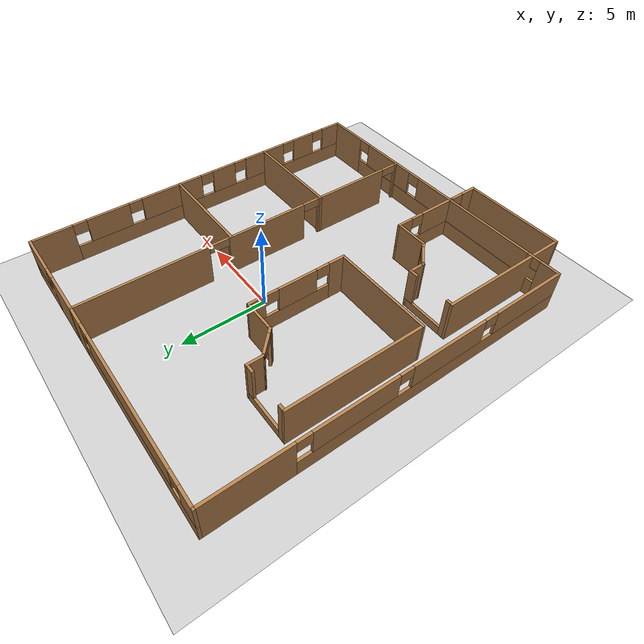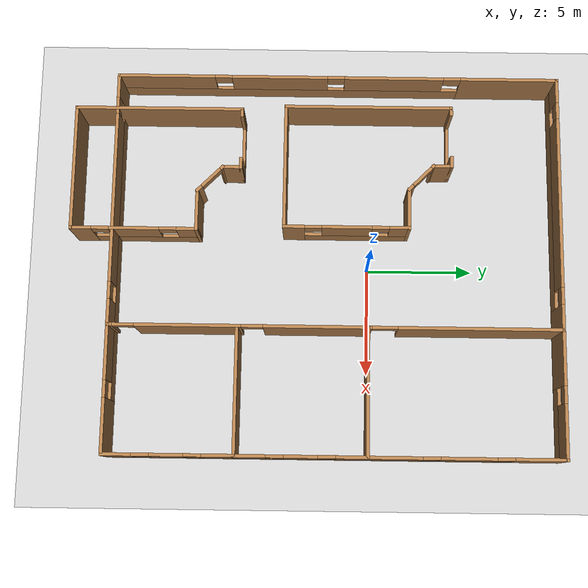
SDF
<?xml version="1.0" ?>
<sdf version='1.6'>
  <world name='default'>
    <model name='ground_plane'>
      <static>1</static>
      <link name='link'>
        <collision name='collision'>
          <geometry>
            <plane>
              <normal>0 0 1</normal>
              <size>100 100</size>
            </plane>
          </geometry>
          <surface>
            <contact>
              <collide_bitmask>65535</collide_bitmask>
              <ode/>
            </contact>
            <friction>
              <ode>
                <mu>100</mu>
                <mu2>50</mu2>
              </ode>
              <torsional>
                <ode/>
              </torsional>
            </friction>
            <bounce/>
          </surface>
          <max_contacts>10</max_contacts>
        </collision>
        <visual name='visual'>
          <cast_shadows>0</cast_shadows>
          <geometry>
            <plane>
              <normal>0 0 1</normal>
              <size>100 100</size>
            </plane>
          </geometry>
          <material>
            <script>
              <uri>file://media/materials/scripts/gazebo.material</uri>
              <name>Gazebo/Grey</name>
            </script>
          </material>
        </visual>
        <self_collide>0</self_collide>
        <enable_wind>0</enable_wind>
        <kinematic>0</kinematic>
      </link>
    </model>
    <scene>
      <ambient>0.4 0.4 0.4 1</ambient>
      <background>0.7 0.7 0.7 1</background>
      <shadows>1</shadows>
    </scene>

    <model name='hospital_room_empty'>
      <link name='Wall_0'>
        <pose frame=''>-4e-06 -3.9165 0 0 -0 0</pose>
        <self_collide>0</self_collide>
        <enable_wind>0</enable_wind>
        <kinematic>0</kinematic>
        <visual name='Wall_0_Visual'>
          <pose frame=''>0 0 1.25 0 -0 0</pose>
          <geometry>
            <box>
              <size>6 0.15 2.5</size>
            </box>
          </geometry>
          <material>
            <script>
              <uri>file://media/materials/scripts/gazebo.material</uri>
              <name>Gazebo/Wood</name>
            </script>
            <ambient>1 1 1 1</ambient>
          </material>
          <meta>
            <layer>0</layer>
          </meta>
          <transparency>0</transparency>
          <cast_shadows>1</cast_shadows>
        </visual>
        <collision name='Wall_0_Collision'>
          <laser_retro>0</laser_retro>
          <max_contacts>10</max_contacts>
          <pose frame=''>0 0 1.25 0 -0 0</pose>
          <geometry>
            <box>
              <size>6 0.15 2.5</size>
            </box>
          </geometry>
          <surface>
            <friction>
              <ode>
                <mu>1</mu>
                <mu2>1</mu2>
                <fdir1>0 0 0</fdir1>
                <slip1>0</slip1>
                <slip2>0</slip2>
              </ode>
              <torsional>
                <coefficient>1</coefficient>
                <patch_radius>0</patch_radius>
                <surface_radius>0</surface_radius>
                <use_patch_radius>1</use_patch_radius>
                <ode>
                  <slip>0</slip>
                </ode>
              </torsional>
            </friction>
            <bounce>
              <restitution_coefficient>0</restitution_coefficient>
              <threshold>1e+06</threshold>
            </bounce>
            <contact>
              <collide_without_contact>0</collide_without_contact>
              <collide_without_contact_bitmask>1</collide_without_contact_bitmask>
              <collide_bitmask>1</collide_bitmask>
              <ode>
                <soft_cfm>0</soft_cfm>
                <soft_erp>0.2</soft_erp>
                <kp>1e+13</kp>
                <kd>1</kd>
                <max_vel>0.01</max_vel>
                <min_depth>0</min_depth>
              </ode>
              <bullet>
                <split_impulse>1</split_impulse>
                <split_impulse_penetration_threshold>-0.01</split_impulse_penetration_threshold>
                <soft_cfm>0</soft_cfm>
                <soft_erp>0.2</soft_erp>
                <kp>1e+13</kp>
                <kd>1</kd>
              </bullet>
            </contact>
          </surface>
        </collision>
      </link>
      <link name='Wall_3'>
        <pose frame=''>-2.925 0 0 0 -0 1.5708</pose>
        <self_collide>0</self_collide>
        <enable_wind>0</enable_wind>
        <kinematic>0</kinematic>
        <visual name='Wall_3_Visual'>
          <pose frame=''>0 0 1.25 0 -0 0</pose>
          <geometry>
            <box>
              <size>7.98302 0.15 2.5</size>
            </box>
          </geometry>
          <material>
            <script>
              <uri>file://media/materials/scripts/gazebo.material</uri>
              <name>Gazebo/Wood</name>
            </script>
            <ambient>1 1 1 1</ambient>
          </material>
          <meta>
            <layer>0</layer>
          </meta>
          <transparency>0</transparency>
          <cast_shadows>1</cast_shadows>
        </visual>
        <collision name='Wall_3_Collision'>
          <laser_retro>0</laser_retro>
          <max_contacts>10</max_contacts>
          <pose frame=''>0 0 1.25 0 -0 0</pose>
          <geometry>
            <box>
              <size>7.98302 0.15 2.5</size>
            </box>
          </geometry>
          <surface>
            <friction>
              <ode>
                <mu>1</mu>
                <mu2>1</mu2>
                <fdir1>0 0 0</fdir1>
                <slip1>0</slip1>
                <slip2>0</slip2>
              </ode>
              <torsional>
                <coefficient>1</coefficient>
                <patch_radius>0</patch_radius>
                <surface_radius>0</surface_radius>
                <use_patch_radius>1</use_patch_radius>
                <ode>
                  <slip>0</slip>
                </ode>
              </torsional>
            </friction>
            <bounce>
              <restitution_coefficient>0</restitution_coefficient>
              <threshold>1e+06</threshold>
            </bounce>
            <contact>
              <collide_without_contact>0</collide_without_contact>
              <collide_without_contact_bitmask>1</collide_without_contact_bitmask>
              <collide_bitmask>1</collide_bitmask>
              <ode>
                <soft_cfm>0</soft_cfm>
                <soft_erp>0.2</soft_erp>
                <kp>1e+13</kp>
                <kd>1</kd>
                <max_vel>0.01</max_vel>
                <min_depth>0</min_depth>
              </ode>
              <bullet>
                <split_impulse>1</split_impulse>
                <split_impulse_penetration_threshold>-0.01</split_impulse_penetration_threshold>
                <soft_cfm>0</soft_cfm>
                <soft_erp>0.2</soft_erp>
                <kp>1e+13</kp>
                <kd>1</kd>
              </bullet>
            </contact>
          </surface>
        </collision>
      </link>
      <link name='Wall_4'>
        <pose frame=''>-1.5 3.9165 0 0 -0 0</pose>
        <self_collide>0</self_collide>
        <enable_wind>0</enable_wind>
        <kinematic>0</kinematic>
        <visual name='Wall_4_Visual_0'>
          <pose frame=''>-1.28125 0 1.25 0 -0 0</pose>
          <geometry>
            <box>
              <size>0.437506 0.15 2.5</size>
            </box>
          </geometry>
          <material>
            <script>
              <uri>file://media/materials/scripts/gazebo.material</uri>
              <name>Gazebo/Wood</name>
            </script>
            <ambient>1 1 1 1</ambient>
          </material>
          <meta>
            <layer>0</layer>
          </meta>
          <transparency>0</transparency>
          <cast_shadows>1</cast_shadows>
        </visual>
        <visual name='Wall_4_Visual_1'>
          <pose frame=''>0.218753 0 0.25 0 -0 0</pose>
          <geometry>
            <box>
              <size>2.56249 0.15 0.5</size>
            </box>
          </geometry>
          <material>
            <script>
              <uri>file://media/materials/scripts/gazebo.material</uri>
              <name>Gazebo/Wood</name>
            </script>
            <ambient>1 1 1 1</ambient>
          </material>
          <meta>
            <layer>0</layer>
          </meta>
          <transparency>0</transparency>
          <cast_shadows>1</cast_shadows>
        </visual>
        <visual name='Wall_4_Visual_2'>
          <pose frame=''>1.21875 0 1.5 0 -0 0</pose>
          <geometry>
            <box>
              <size>0.562494 0.15 2</size>
            </box>
          </geometry>
          <material>
            <script>
              <uri>file://media/materials/scripts/gazebo.material</uri>
              <name>Gazebo/Wood</name>
            </script>
            <ambient>1 1 1 1</ambient>
          </material>
          <meta>
            <layer>0</layer>
          </meta>
          <transparency>0</transparency>
          <cast_shadows>1</cast_shadows>
        </visual>
        <collision name='Wall_4_Collision_0'>
          <laser_retro>0</laser_retro>
          <max_contacts>10</max_contacts>
          <pose frame=''>-1.28125 0 1.25 0 -0 0</pose>
          <geometry>
            <box>
              <size>0.437506 0.15 2.5</size>
            </box>
          </geometry>
          <surface>
            <friction>
              <ode>
                <mu>1</mu>
                <mu2>1</mu2>
                <fdir1>0 0 0</fdir1>
                <slip1>0</slip1>
                <slip2>0</slip2>
              </ode>
              <torsional>
                <coefficient>1</coefficient>
                <patch_radius>0</patch_radius>
                <surface_radius>0</surface_radius>
                <use_patch_radius>1</use_patch_radius>
                <ode>
                  <slip>0</slip>
                </ode>
              </torsional>
            </friction>
            <bounce>
              <restitution_coefficient>0</restitution_coefficient>
              <threshold>1e+06</threshold>
            </bounce>
            <contact>
              <collide_without_contact>0</collide_without_contact>
              <collide_without_contact_bitmask>1</collide_without_contact_bitmask>
              <collide_bitmask>1</collide_bitmask>
              <ode>
                <soft_cfm>0</soft_cfm>
                <soft_erp>0.2</soft_erp>
                <kp>1e+13</kp>
                <kd>1</kd>
                <max_vel>0.01</max_vel>
                <min_depth>0</min_depth>
              </ode>
              <bullet>
                <split_impulse>1</split_impulse>
                <split_impulse_penetration_threshold>-0.01</split_impulse_penetration_threshold>
                <soft_cfm>0</soft_cfm>
                <soft_erp>0.2</soft_erp>
                <kp>1e+13</kp>
                <kd>1</kd>
              </bullet>
            </contact>
          </surface>
        </collision>
        <collision name='Wall_4_Collision_1'>
          <laser_retro>0</laser_retro>
          <max_contacts>10</max_contacts>
          <pose frame=''>0.218753 0 0.25 0 -0 0</pose>
          <geometry>
            <box>
              <size>2.56249 0.15 0.5</size>
            </box>
          </geometry>
          <surface>
            <friction>
              <ode>
                <mu>1</mu>
                <mu2>1</mu2>
                <fdir1>0 0 0</fdir1>
                <slip1>0</slip1>
                <slip2>0</slip2>
              </ode>
              <torsional>
                <coefficient>1</coefficient>
                <patch_radius>0</patch_radius>
                <surface_radius>0</surface_radius>
                <use_patch_radius>1</use_patch_radius>
                <ode>
                  <slip>0</slip>
                </ode>
              </torsional>
            </friction>
            <bounce>
              <restitution_coefficient>0</restitution_coefficient>
              <threshold>1e+06</threshold>
            </bounce>
            <contact>
              <collide_without_contact>0</collide_without_contact>
              <collide_without_contact_bitmask>1</collide_without_contact_bitmask>
              <collide_bitmask>1</collide_bitmask>
              <ode>
                <soft_cfm>0</soft_cfm>
                <soft_erp>0.2</soft_erp>
                <kp>1e+13</kp>
                <kd>1</kd>
                <max_vel>0.01</max_vel>
                <min_depth>0</min_depth>
              </ode>
              <bullet>
                <split_impulse>1</split_impulse>
                <split_impulse_penetration_threshold>-0.01</split_impulse_penetration_threshold>
                <soft_cfm>0</soft_cfm>
                <soft_erp>0.2</soft_erp>
                <kp>1e+13</kp>
                <kd>1</kd>
              </bullet>
            </contact>
          </surface>
        </collision>
        <collision name='Wall_4_Collision_2'>
          <laser_retro>0</laser_retro>
          <max_contacts>10</max_contacts>
          <pose frame=''>1.21875 0 1.5 0 -0 0</pose>
          <geometry>
            <box>
              <size>0.562494 0.15 2</size>
            </box>
          </geometry>
          <surface>
            <friction>
              <ode>
                <mu>1</mu>
                <mu2>1</mu2>
                <fdir1>0 0 0</fdir1>
                <slip1>0</slip1>
                <slip2>0</slip2>
              </ode>
              <torsional>
                <coefficient>1</coefficient>
                <patch_radius>0</patch_radius>
                <surface_radius>0</surface_radius>
                <use_patch_radius>1</use_patch_radius>
                <ode>
                  <slip>0</slip>
                </ode>
              </torsional>
            </friction>
            <bounce>
              <restitution_coefficient>0</restitution_coefficient>
              <threshold>1e+06</threshold>
            </bounce>
            <contact>
              <collide_without_contact>0</collide_without_contact>
              <collide_without_contact_bitmask>1</collide_without_contact_bitmask>
              <collide_bitmask>1</collide_bitmask>
              <ode>
                <soft_cfm>0</soft_cfm>
                <soft_erp>0.2</soft_erp>
                <kp>1e+13</kp>
                <kd>1</kd>
                <max_vel>0.01</max_vel>
                <min_depth>0</min_depth>
              </ode>
              <bullet>
                <split_impulse>1</split_impulse>
                <split_impulse_penetration_threshold>-0.01</split_impulse_penetration_threshold>
                <soft_cfm>0</soft_cfm>
                <soft_erp>0.2</soft_erp>
                <kp>1e+13</kp>
                <kd>1</kd>
              </bullet>
            </contact>
          </surface>
        </collision>
      </link>
      <link name='Wall_5'>
        <pose frame=''>-0.075004 3.4915 0 0 0 -1.5708</pose>
        <self_collide>0</self_collide>
        <enable_wind>0</enable_wind>
        <kinematic>0</kinematic>
        <visual name='Wall_5_Visual'>
          <pose frame=''>0 0 1.25 0 -0 0</pose>
          <geometry>
            <box>
              <size>1 0.15 2.5</size>
            </box>
          </geometry>
          <material>
            <script>
              <uri>file://media/materials/scripts/gazebo.material</uri>
              <name>Gazebo/Wood</name>
            </script>
            <ambient>1 1 1 1</ambient>
          </material>
          <meta>
            <layer>0</layer>
          </meta>
          <transparency>0</transparency>
          <cast_shadows>1</cast_shadows>
        </visual>
        <collision name='Wall_5_Collision'>
          <laser_retro>0</laser_retro>
          <max_contacts>10</max_contacts>
          <pose frame=''>0 0 1.25 0 -0 0</pose>
          <geometry>
            <box>
              <size>1 0.15 2.5</size>
            </box>
          </geometry>
          <surface>
            <friction>
              <ode>
                <mu>1</mu>
                <mu2>1</mu2>
                <fdir1>0 0 0</fdir1>
                <slip1>0</slip1>
                <slip2>0</slip2>
              </ode>
              <torsional>
                <coefficient>1</coefficient>
                <patch_radius>0</patch_radius>
                <surface_radius>0</surface_radius>
                <use_patch_radius>1</use_patch_radius>
                <ode>
                  <slip>0</slip>
                </ode>
              </torsional>
            </friction>
            <bounce>
              <restitution_coefficient>0</restitution_coefficient>
              <threshold>1e+06</threshold>
            </bounce>
            <contact>
              <collide_without_contact>0</collide_without_contact>
              <collide_without_contact_bitmask>1</collide_without_contact_bitmask>
              <collide_bitmask>1</collide_bitmask>
              <ode>
                <soft_cfm>0</soft_cfm>
                <soft_erp>0.2</soft_erp>
                <kp>1e+13</kp>
                <kd>1</kd>
                <max_vel>0.01</max_vel>
                <min_depth>0</min_depth>
              </ode>
              <bullet>
                <split_impulse>1</split_impulse>
                <split_impulse_penetration_threshold>-0.01</split_impulse_penetration_threshold>
                <soft_cfm>0</soft_cfm>
                <soft_erp>0.2</soft_erp>
                <kp>1e+13</kp>
                <kd>1</kd>
              </bullet>
            </contact>
          </surface>
        </collision>
      </link>
      <link name='Wall_7'>
        <pose frame=''>2.925 -1 0 0 -0 1.5708</pose>
        <self_collide>0</self_collide>
        <enable_wind>0</enable_wind>
        <kinematic>0</kinematic>
        <visual name='Wall_7_Visual_0'>
          <pose frame=''>-2.47597 0 1.25 0 -0 0</pose>
          <geometry>
            <box>
              <size>1.03106 0.15 2.5</size>
            </box>
          </geometry>
          <material>
            <script>
              <uri>file://media/materials/scripts/gazebo.material</uri>
              <name>Gazebo/Wood</name>
            </script>
            <ambient>0.921569 0.807843 0.615686 1</ambient>
          </material>
          <meta>
            <layer>0</layer>
          </meta>
          <transparency>0</transparency>
          <cast_shadows>1</cast_shadows>
        </visual>
        <visual name='Wall_7_Visual_1'>
          <pose frame=''>0.515531 0 0.5 0 -0 0</pose>
          <geometry>
            <box>
              <size>4.95194 0.15 1</size>
            </box>
          </geometry>
          <material>
            <script>
              <uri>file://media/materials/scripts/gazebo.material</uri>
              <name>Gazebo/Wood</name>
            </script>
            <ambient>0.921569 0.807843 0.615686 1</ambient>
          </material>
          <meta>
            <layer>0</layer>
          </meta>
          <transparency>0</transparency>
          <cast_shadows>1</cast_shadows>
        </visual>
        <visual name='Wall_7_Visual_2'>
          <pose frame=''>0.016139 0 1.75 0 -0 0</pose>
          <geometry>
            <box>
              <size>2.35315 0.15 1.5</size>
            </box>
          </geometry>
          <material>
            <script>
              <uri>file://media/materials/scripts/gazebo.material</uri>
              <name>Gazebo/Wood</name>
            </script>
            <ambient>0.921569 0.807843 0.615686 1</ambient>
          </material>
          <meta>
            <layer>0</layer>
          </meta>
          <transparency>0</transparency>
          <cast_shadows>1</cast_shadows>
        </visual>
        <visual name='Wall_7_Visual_3'>
          <pose frame=''>2.49211 0 1.75 0 -0 0</pose>
          <geometry>
            <box>
              <size>0.998785 0.15 1.5</size>
            </box>
          </geometry>
          <material>
            <script>
              <uri>file://media/materials/scripts/gazebo.material</uri>
              <name>Gazebo/Wood</name>
            </script>
            <ambient>0.921569 0.807843 0.615686 1</ambient>
          </material>
          <meta>
            <layer>0</layer>
          </meta>
          <transparency>0</transparency>
          <cast_shadows>1</cast_shadows>
        </visual>
        <visual name='Wall_7_Visual_4'>
          <pose frame=''>-1.56044 0 2.15 0 -0 0</pose>
          <geometry>
            <box>
              <size>0.8 0.15 0.7</size>
            </box>
          </geometry>
          <material>
            <script>
              <uri>file://media/materials/scripts/gazebo.material</uri>
              <name>Gazebo/Wood</name>
            </script>
            <ambient>0.921569 0.807843 0.615686 1</ambient>
          </material>
          <meta>
            <layer>0</layer>
          </meta>
          <transparency>0</transparency>
          <cast_shadows>1</cast_shadows>
        </visual>
        <visual name='Wall_7_Visual_5'>
          <pose frame=''>1.59272 0 2.15 0 -0 0</pose>
          <geometry>
            <box>
              <size>0.8 0.15 0.7</size>
            </box>
          </geometry>
          <material>
            <script>
              <uri>file://media/materials/scripts/gazebo.material</uri>
              <name>Gazebo/Wood</name>
            </script>
            <ambient>0.921569 0.807843 0.615686 1</ambient>
          </material>
          <meta>
            <layer>0</layer>
          </meta>
          <transparency>0</transparency>
          <cast_shadows>1</cast_shadows>
        </visual>
        <collision name='Wall_7_Collision_0'>
          <laser_retro>0</laser_retro>
          <max_contacts>10</max_contacts>
          <pose frame=''>-2.47597 0 1.25 0 -0 0</pose>
          <geometry>
            <box>
              <size>1.03106 0.15 2.5</size>
            </box>
          </geometry>
          <surface>
            <friction>
              <ode>
                <mu>1</mu>
                <mu2>1</mu2>
                <fdir1>0 0 0</fdir1>
                <slip1>0</slip1>
                <slip2>0</slip2>
              </ode>
              <torsional>
                <coefficient>1</coefficient>
                <patch_radius>0</patch_radius>
                <surface_radius>0</surface_radius>
                <use_patch_radius>1</use_patch_radius>
                <ode>
                  <slip>0</slip>
                </ode>
              </torsional>
            </friction>
            <bounce>
              <restitution_coefficient>0</restitution_coefficient>
              <threshold>1e+06</threshold>
            </bounce>
            <contact>
              <collide_without_contact>0</collide_without_contact>
              <collide_without_contact_bitmask>1</collide_without_contact_bitmask>
              <collide_bitmask>1</collide_bitmask>
              <ode>
                <soft_cfm>0</soft_cfm>
                <soft_erp>0.2</soft_erp>
                <kp>1e+13</kp>
                <kd>1</kd>
                <max_vel>0.01</max_vel>
                <min_depth>0</min_depth>
              </ode>
              <bullet>
                <split_impulse>1</split_impulse>
                <split_impulse_penetration_threshold>-0.01</split_impulse_penetration_threshold>
                <soft_cfm>0</soft_cfm>
                <soft_erp>0.2</soft_erp>
                <kp>1e+13</kp>
                <kd>1</kd>
              </bullet>
            </contact>
          </surface>
        </collision>
        <collision name='Wall_7_Collision_1'>
          <laser_retro>0</laser_retro>
          <max_contacts>10</max_contacts>
          <pose frame=''>0.515531 0 0.5 0 -0 0</pose>
          <geometry>
            <box>
              <size>4.95194 0.15 1</size>
            </box>
          </geometry>
          <surface>
            <friction>
              <ode>
                <mu>1</mu>
                <mu2>1</mu2>
                <fdir1>0 0 0</fdir1>
                <slip1>0</slip1>
                <slip2>0</slip2>
              </ode>
              <torsional>
                <coefficient>1</coefficient>
                <patch_radius>0</patch_radius>
                <surface_radius>0</surface_radius>
                <use_patch_radius>1</use_patch_radius>
                <ode>
                  <slip>0</slip>
                </ode>
              </torsional>
            </friction>
            <bounce>
              <restitution_coefficient>0</restitution_coefficient>
              <threshold>1e+06</threshold>
            </bounce>
            <contact>
              <collide_without_contact>0</collide_without_contact>
              <collide_without_contact_bitmask>1</collide_without_contact_bitmask>
              <collide_bitmask>1</collide_bitmask>
              <ode>
                <soft_cfm>0</soft_cfm>
                <soft_erp>0.2</soft_erp>
                <kp>1e+13</kp>
                <kd>1</kd>
                <max_vel>0.01</max_vel>
                <min_depth>0</min_depth>
              </ode>
              <bullet>
                <split_impulse>1</split_impulse>
                <split_impulse_penetration_threshold>-0.01</split_impulse_penetration_threshold>
                <soft_cfm>0</soft_cfm>
                <soft_erp>0.2</soft_erp>
                <kp>1e+13</kp>
                <kd>1</kd>
              </bullet>
            </contact>
          </surface>
        </collision>
        <collision name='Wall_7_Collision_2'>
          <laser_retro>0</laser_retro>
          <max_contacts>10</max_contacts>
          <pose frame=''>0.016139 0 1.75 0 -0 0</pose>
          <geometry>
            <box>
              <size>2.35315 0.15 1.5</size>
            </box>
          </geometry>
          <surface>
            <friction>
              <ode>
                <mu>1</mu>
                <mu2>1</mu2>
                <fdir1>0 0 0</fdir1>
                <slip1>0</slip1>
                <slip2>0</slip2>
              </ode>
              <torsional>
                <coefficient>1</coefficient>
                <patch_radius>0</patch_radius>
                <surface_radius>0</surface_radius>
                <use_patch_radius>1</use_patch_radius>
                <ode>
                  <slip>0</slip>
                </ode>
              </torsional>
            </friction>
            <bounce>
              <restitution_coefficient>0</restitution_coefficient>
              <threshold>1e+06</threshold>
            </bounce>
            <contact>
              <collide_without_contact>0</collide_without_contact>
              <collide_without_contact_bitmask>1</collide_without_contact_bitmask>
              <collide_bitmask>1</collide_bitmask>
              <ode>
                <soft_cfm>0</soft_cfm>
                <soft_erp>0.2</soft_erp>
                <kp>1e+13</kp>
                <kd>1</kd>
                <max_vel>0.01</max_vel>
                <min_depth>0</min_depth>
              </ode>
              <bullet>
                <split_impulse>1</split_impulse>
                <split_impulse_penetration_threshold>-0.01</split_impulse_penetration_threshold>
                <soft_cfm>0</soft_cfm>
                <soft_erp>0.2</soft_erp>
                <kp>1e+13</kp>
                <kd>1</kd>
              </bullet>
            </contact>
          </surface>
        </collision>
        <collision name='Wall_7_Collision_3'>
          <laser_retro>0</laser_retro>
          <max_contacts>10</max_contacts>
          <pose frame=''>2.49211 0 1.75 0 -0 0</pose>
          <geometry>
            <box>
              <size>0.998785 0.15 1.5</size>
            </box>
          </geometry>
          <surface>
            <friction>
              <ode>
                <mu>1</mu>
                <mu2>1</mu2>
                <fdir1>0 0 0</fdir1>
                <slip1>0</slip1>
                <slip2>0</slip2>
              </ode>
              <torsional>
                <coefficient>1</coefficient>
                <patch_radius>0</patch_radius>
                <surface_radius>0</surface_radius>
                <use_patch_radius>1</use_patch_radius>
                <ode>
                  <slip>0</slip>
                </ode>
              </torsional>
            </friction>
            <bounce>
              <restitution_coefficient>0</restitution_coefficient>
              <threshold>1e+06</threshold>
            </bounce>
            <contact>
              <collide_without_contact>0</collide_without_contact>
              <collide_without_contact_bitmask>1</collide_without_contact_bitmask>
              <collide_bitmask>1</collide_bitmask>
              <ode>
                <soft_cfm>0</soft_cfm>
                <soft_erp>0.2</soft_erp>
                <kp>1e+13</kp>
                <kd>1</kd>
                <max_vel>0.01</max_vel>
                <min_depth>0</min_depth>
              </ode>
              <bullet>
                <split_impulse>1</split_impulse>
                <split_impulse_penetration_threshold>-0.01</split_impulse_penetration_threshold>
                <soft_cfm>0</soft_cfm>
                <soft_erp>0.2</soft_erp>
                <kp>1e+13</kp>
                <kd>1</kd>
              </bullet>
            </contact>
          </surface>
        </collision>
        <collision name='Wall_7_Collision_4'>
          <laser_retro>0</laser_retro>
          <max_contacts>10</max_contacts>
          <pose frame=''>-1.56044 0 2.15 0 -0 0</pose>
          <geometry>
            <box>
              <size>0.8 0.15 0.7</size>
            </box>
          </geometry>
          <surface>
            <friction>
              <ode>
                <mu>1</mu>
                <mu2>1</mu2>
                <fdir1>0 0 0</fdir1>
                <slip1>0</slip1>
                <slip2>0</slip2>
              </ode>
              <torsional>
                <coefficient>1</coefficient>
                <patch_radius>0</patch_radius>
                <surface_radius>0</surface_radius>
                <use_patch_radius>1</use_patch_radius>
                <ode>
                  <slip>0</slip>
                </ode>
              </torsional>
            </friction>
            <bounce>
              <restitution_coefficient>0</restitution_coefficient>
              <threshold>1e+06</threshold>
            </bounce>
            <contact>
              <collide_without_contact>0</collide_without_contact>
              <collide_without_contact_bitmask>1</collide_without_contact_bitmask>
              <collide_bitmask>1</collide_bitmask>
              <ode>
                <soft_cfm>0</soft_cfm>
                <soft_erp>0.2</soft_erp>
                <kp>1e+13</kp>
                <kd>1</kd>
                <max_vel>0.01</max_vel>
                <min_depth>0</min_depth>
              </ode>
              <bullet>
                <split_impulse>1</split_impulse>
                <split_impulse_penetration_threshold>-0.01</split_impulse_penetration_threshold>
                <soft_cfm>0</soft_cfm>
                <soft_erp>0.2</soft_erp>
                <kp>1e+13</kp>
                <kd>1</kd>
              </bullet>
            </contact>
          </surface>
        </collision>
        <collision name='Wall_7_Collision_5'>
          <laser_retro>0</laser_retro>
          <max_contacts>10</max_contacts>
          <pose frame=''>1.59272 0 2.15 0 -0 0</pose>
          <geometry>
            <box>
              <size>0.8 0.15 0.7</size>
            </box>
          </geometry>
          <surface>
            <friction>
              <ode>
                <mu>1</mu>
                <mu2>1</mu2>
                <fdir1>0 0 0</fdir1>
                <slip1>0</slip1>
                <slip2>0</slip2>
              </ode>
              <torsional>
                <coefficient>1</coefficient>
                <patch_radius>0</patch_radius>
                <surface_radius>0</surface_radius>
                <use_patch_radius>1</use_patch_radius>
                <ode>
                  <slip>0</slip>
                </ode>
              </torsional>
            </friction>
            <bounce>
              <restitution_coefficient>0</restitution_coefficient>
              <threshold>1e+06</threshold>
            </bounce>
            <contact>
              <collide_without_contact>0</collide_without_contact>
              <collide_without_contact_bitmask>1</collide_without_contact_bitmask>
              <collide_bitmask>1</collide_bitmask>
              <ode>
                <soft_cfm>0</soft_cfm>
                <soft_erp>0.2</soft_erp>
                <kp>1e+13</kp>
                <kd>1</kd>
                <max_vel>0.01</max_vel>
                <min_depth>0</min_depth>
              </ode>
              <bullet>
                <split_impulse>1</split_impulse>
                <split_impulse_penetration_threshold>-0.01</split_impulse_penetration_threshold>
                <soft_cfm>0</soft_cfm>
                <soft_erp>0.2</soft_erp>
                <kp>1e+13</kp>
                <kd>1</kd>
              </bullet>
            </contact>
          </surface>
        </collision>
      </link>
      <link name='Wall_8'>
        <pose frame=''>2 1.9166 0 0 -0 3.14148</pose>
        <self_collide>0</self_collide>
        <enable_wind>0</enable_wind>
        <kinematic>0</kinematic>
        <visual name='Wall_8_Visual'>
          <pose frame=''>0 0 1.25 0 -0 0</pose>
          <geometry>
            <box>
              <size>2 0.15 2.5</size>
            </box>
          </geometry>
          <material>
            <script>
              <uri>file://media/materials/scripts/gazebo.material</uri>
              <name>Gazebo/Wood</name>
            </script>
            <ambient>1 1 1 1</ambient>
          </material>
          <meta>
            <layer>0</layer>
          </meta>
          <transparency>0</transparency>
          <cast_shadows>1</cast_shadows>
        </visual>
        <collision name='Wall_8_Collision'>
          <laser_retro>0</laser_retro>
          <max_contacts>10</max_contacts>
          <pose frame=''>0 0 1.25 0 -0 0</pose>
          <geometry>
            <box>
              <size>2 0.15 2.5</size>
            </box>
          </geometry>
          <surface>
            <friction>
              <ode>
                <mu>1</mu>
                <mu2>1</mu2>
                <fdir1>0 0 0</fdir1>
                <slip1>0</slip1>
                <slip2>0</slip2>
              </ode>
              <torsional>
                <coefficient>1</coefficient>
                <patch_radius>0</patch_radius>
                <surface_radius>0</surface_radius>
                <use_patch_radius>1</use_patch_radius>
                <ode>
                  <slip>0</slip>
                </ode>
              </torsional>
            </friction>
            <bounce>
              <restitution_coefficient>0</restitution_coefficient>
              <threshold>1e+06</threshold>
            </bounce>
            <contact>
              <collide_without_contact>0</collide_without_contact>
              <collide_without_contact_bitmask>1</collide_without_contact_bitmask>
              <collide_bitmask>1</collide_bitmask>
              <ode>
                <soft_cfm>0</soft_cfm>
                <soft_erp>0.2</soft_erp>
                <kp>1e+13</kp>
                <kd>1</kd>
                <max_vel>0.01</max_vel>
                <min_depth>0</min_depth>
              </ode>
              <bullet>
                <split_impulse>1</split_impulse>
                <split_impulse_penetration_threshold>-0.01</split_impulse_penetration_threshold>
                <soft_cfm>0</soft_cfm>
                <soft_erp>0.2</soft_erp>
                <kp>1e+13</kp>
                <kd>1</kd>
              </bullet>
            </contact>
          </surface>
        </collision>
      </link>
      <link name='Wall_9'>
        <pose frame=''>0.499996 2.4916 0 0 -0 2.35628</pose>
        <self_collide>0</self_collide>
        <enable_wind>0</enable_wind>
        <kinematic>0</kinematic>
        <visual name='Wall_9_Visual_1'>
          <pose frame=''>0.785148 0 1.25 0 -0 0</pose>
          <geometry>
            <box>
              <size>0.205905 0.15 2.5</size>
            </box>
          </geometry>
          <material>
            <script>
              <uri>file://media/materials/scripts/gazebo.material</uri>
              <name>Gazebo/Wood</name>
            </script>
            <ambient>1 1 1 1</ambient>
          </material>
          <meta>
            <layer>0</layer>
          </meta>
          <transparency>0</transparency>
          <cast_shadows>1</cast_shadows>
        </visual>
        <visual name='Wall_9_Visual_0'>
          <pose frame=''>-0.702952 0 1.25 0 -0 0</pose>
          <geometry>
            <box>
              <size>0.370295 0.15 2.5</size>
            </box>
          </geometry>
          <material>
            <script>
              <uri>file://media/materials/scripts/gazebo.material</uri>
              <name>Gazebo/Wood</name>
            </script>
            <ambient>1 1 1 1</ambient>
          </material>
          <meta>
            <layer>0</layer>
          </meta>
          <transparency>0</transparency>
          <cast_shadows>1</cast_shadows>
        </visual>
        <visual name='Wall_9_Visual_2'>
          <pose frame=''>0.082195 0 2.25 0 -0 0</pose>
          <geometry>
            <box>
              <size>1.2 0.15 0.5</size>
            </box>
          </geometry>
          <material>
            <script>
              <uri>file://media/materials/scripts/gazebo.material</uri>
              <name>Gazebo/Wood</name>
            </script>
            <ambient>1 1 1 1</ambient>
          </material>
          <meta>
            <layer>0</layer>
          </meta>
          <transparency>0</transparency>
          <cast_shadows>1</cast_shadows>
        </visual>
        <collision name='Wall_9_Collision_0'>
          <laser_retro>0</laser_retro>
          <max_contacts>10</max_contacts>
          <pose frame=''>-0.702952 0 1.25 0 -0 0</pose>
          <geometry>
            <box>
              <size>0.370295 0.15 2.5</size>
            </box>
          </geometry>
          <surface>
            <friction>
              <ode>
                <mu>1</mu>
                <mu2>1</mu2>
                <fdir1>0 0 0</fdir1>
                <slip1>0</slip1>
                <slip2>0</slip2>
              </ode>
              <torsional>
                <coefficient>1</coefficient>
                <patch_radius>0</patch_radius>
                <surface_radius>0</surface_radius>
                <use_patch_radius>1</use_patch_radius>
                <ode>
                  <slip>0</slip>
                </ode>
              </torsional>
            </friction>
            <bounce>
              <restitution_coefficient>0</restitution_coefficient>
              <threshold>1e+06</threshold>
            </bounce>
            <contact>
              <collide_without_contact>0</collide_without_contact>
              <collide_without_contact_bitmask>1</collide_without_contact_bitmask>
              <collide_bitmask>1</collide_bitmask>
              <ode>
                <soft_cfm>0</soft_cfm>
                <soft_erp>0.2</soft_erp>
                <kp>1e+13</kp>
                <kd>1</kd>
                <max_vel>0.01</max_vel>
                <min_depth>0</min_depth>
              </ode>
              <bullet>
                <split_impulse>1</split_impulse>
                <split_impulse_penetration_threshold>-0.01</split_impulse_penetration_threshold>
                <soft_cfm>0</soft_cfm>
                <soft_erp>0.2</soft_erp>
                <kp>1e+13</kp>
                <kd>1</kd>
              </bullet>
            </contact>
          </surface>
        </collision>
        <collision name='Wall_9_Collision_1'>
          <laser_retro>0</laser_retro>
          <max_contacts>10</max_contacts>
          <pose frame=''>0.785148 0 1.25 0 -0 0</pose>
          <geometry>
            <box>
              <size>0.205905 0.15 2.5</size>
            </box>
          </geometry>
          <surface>
            <friction>
              <ode>
                <mu>1</mu>
                <mu2>1</mu2>
                <fdir1>0 0 0</fdir1>
                <slip1>0</slip1>
                <slip2>0</slip2>
              </ode>
              <torsional>
                <coefficient>1</coefficient>
                <patch_radius>0</patch_radius>
                <surface_radius>0</surface_radius>
                <use_patch_radius>1</use_patch_radius>
                <ode>
                  <slip>0</slip>
                </ode>
              </torsional>
            </friction>
            <bounce>
              <restitution_coefficient>0</restitution_coefficient>
              <threshold>1e+06</threshold>
            </bounce>
            <contact>
              <collide_without_contact>0</collide_without_contact>
              <collide_without_contact_bitmask>1</collide_without_contact_bitmask>
              <collide_bitmask>1</collide_bitmask>
              <ode>
                <soft_cfm>0</soft_cfm>
                <soft_erp>0.2</soft_erp>
                <kp>1e+13</kp>
                <kd>1</kd>
                <max_vel>0.01</max_vel>
                <min_depth>0</min_depth>
              </ode>
              <bullet>
                <split_impulse>1</split_impulse>
                <split_impulse_penetration_threshold>-0.01</split_impulse_penetration_threshold>
                <soft_cfm>0</soft_cfm>
                <soft_erp>0.2</soft_erp>
                <kp>1e+13</kp>
                <kd>1</kd>
              </bullet>
            </contact>
          </surface>
        </collision>
        <collision name='Wall_9_Collision_2'>
          <laser_retro>0</laser_retro>
          <max_contacts>10</max_contacts>
          <pose frame=''>0.082195 0 2.25 0 -0 0</pose>
          <geometry>
            <box>
              <size>1.2 0.15 0.5</size>
            </box>
          </geometry>
          <surface>
            <friction>
              <ode>
                <mu>1</mu>
                <mu2>1</mu2>
                <fdir1>0 0 0</fdir1>
                <slip1>0</slip1>
                <slip2>0</slip2>
              </ode>
              <torsional>
                <coefficient>1</coefficient>
                <patch_radius>0</patch_radius>
                <surface_radius>0</surface_radius>
                <use_patch_radius>1</use_patch_radius>
                <ode>
                  <slip>0</slip>
                </ode>
              </torsional>
            </friction>
            <bounce>
              <restitution_coefficient>0</restitution_coefficient>
              <threshold>1e+06</threshold>
            </bounce>
            <contact>
              <collide_without_contact>0</collide_without_contact>
              <collide_without_contact_bitmask>1</collide_without_contact_bitmask>
              <collide_bitmask>1</collide_bitmask>
              <ode>
                <soft_cfm>0</soft_cfm>
                <soft_erp>0.2</soft_erp>
                <kp>1e+13</kp>
                <kd>1</kd>
                <max_vel>0.01</max_vel>
                <min_depth>0</min_depth>
              </ode>
              <bullet>
                <split_impulse>1</split_impulse>
                <split_impulse_penetration_threshold>-0.01</split_impulse_penetration_threshold>
                <soft_cfm>0</soft_cfm>
                <soft_erp>0.2</soft_erp>
                <kp>1e+13</kp>
                <kd>1</kd>
              </bullet>
            </contact>
          </surface>
        </collision>
      </link>
      <static>1</static>
      <allow_auto_disable>1</allow_auto_disable>
      <pose frame=''>-4.537 -0.0235 0 0 -0 0</pose>
    </model>
    <model name='hospital_room_empty_clone'>
      <link name='Wall_0'>
        <pose frame=''>-4e-06 -3.9165 0 0 -0 0</pose>
        <self_collide>0</self_collide>
        <enable_wind>0</enable_wind>
        <kinematic>0</kinematic>
        <visual name='Wall_0_Visual'>
          <pose frame=''>0 0 1.25 0 -0 0</pose>
          <geometry>
            <box>
              <size>6 0.15 2.5</size>
            </box>
          </geometry>
          <material>
            <script>
              <uri>file://media/materials/scripts/gazebo.material</uri>
              <name>Gazebo/Wood</name>
            </script>
            <ambient>1 1 1 1</ambient>
          </material>
          <meta>
            <layer>0</layer>
          </meta>
          <transparency>0</transparency>
          <cast_shadows>1</cast_shadows>
        </visual>
        <collision name='Wall_0_Collision'>
          <laser_retro>0</laser_retro>
          <max_contacts>10</max_contacts>
          <pose frame=''>0 0 1.25 0 -0 0</pose>
          <geometry>
            <box>
              <size>6 0.15 2.5</size>
            </box>
          </geometry>
          <surface>
            <friction>
              <ode>
                <mu>1</mu>
                <mu2>1</mu2>
                <fdir1>0 0 0</fdir1>
                <slip1>0</slip1>
                <slip2>0</slip2>
              </ode>
              <torsional>
                <coefficient>1</coefficient>
                <patch_radius>0</patch_radius>
                <surface_radius>0</surface_radius>
                <use_patch_radius>1</use_patch_radius>
                <ode>
                  <slip>0</slip>
                </ode>
              </torsional>
            </friction>
            <bounce>
              <restitution_coefficient>0</restitution_coefficient>
              <threshold>1e+06</threshold>
            </bounce>
            <contact>
              <collide_without_contact>0</collide_without_contact>
              <collide_without_contact_bitmask>1</collide_without_contact_bitmask>
              <collide_bitmask>1</collide_bitmask>
              <ode>
                <soft_cfm>0</soft_cfm>
                <soft_erp>0.2</soft_erp>
                <kp>1e+13</kp>
                <kd>1</kd>
                <max_vel>0.01</max_vel>
                <min_depth>0</min_depth>
              </ode>
              <bullet>
                <split_impulse>1</split_impulse>
                <split_impulse_penetration_threshold>-0.01</split_impulse_penetration_threshold>
                <soft_cfm>0</soft_cfm>
                <soft_erp>0.2</soft_erp>
                <kp>1e+13</kp>
                <kd>1</kd>
              </bullet>
            </contact>
          </surface>
        </collision>
      </link>
      <link name='Wall_3'>
        <pose frame=''>-2.925 0 0 0 -0 1.5708</pose>
        <self_collide>0</self_collide>
        <enable_wind>0</enable_wind>
        <kinematic>0</kinematic>
        <visual name='Wall_3_Visual'>
          <pose frame=''>0 0 1.25 0 -0 0</pose>
          <geometry>
            <box>
              <size>7.98302 0.15 2.5</size>
            </box>
          </geometry>
          <material>
            <script>
              <uri>file://media/materials/scripts/gazebo.material</uri>
              <name>Gazebo/Wood</name>
            </script>
            <ambient>1 1 1 1</ambient>
          </material>
          <meta>
            <layer>0</layer>
          </meta>
          <transparency>0</transparency>
          <cast_shadows>1</cast_shadows>
        </visual>
        <collision name='Wall_3_Collision'>
          <laser_retro>0</laser_retro>
          <max_contacts>10</max_contacts>
          <pose frame=''>0 0 1.25 0 -0 0</pose>
          <geometry>
            <box>
              <size>7.98302 0.15 2.5</size>
            </box>
          </geometry>
          <surface>
            <friction>
              <ode>
                <mu>1</mu>
                <mu2>1</mu2>
                <fdir1>0 0 0</fdir1>
                <slip1>0</slip1>
                <slip2>0</slip2>
              </ode>
              <torsional>
                <coefficient>1</coefficient>
                <patch_radius>0</patch_radius>
                <surface_radius>0</surface_radius>
                <use_patch_radius>1</use_patch_radius>
                <ode>
                  <slip>0</slip>
                </ode>
              </torsional>
            </friction>
            <bounce>
              <restitution_coefficient>0</restitution_coefficient>
              <threshold>1e+06</threshold>
            </bounce>
            <contact>
              <collide_without_contact>0</collide_without_contact>
              <collide_without_contact_bitmask>1</collide_without_contact_bitmask>
              <collide_bitmask>1</collide_bitmask>
              <ode>
                <soft_cfm>0</soft_cfm>
                <soft_erp>0.2</soft_erp>
                <kp>1e+13</kp>
                <kd>1</kd>
                <max_vel>0.01</max_vel>
                <min_depth>0</min_depth>
              </ode>
              <bullet>
                <split_impulse>1</split_impulse>
                <split_impulse_penetration_threshold>-0.01</split_impulse_penetration_threshold>
                <soft_cfm>0</soft_cfm>
                <soft_erp>0.2</soft_erp>
                <kp>1e+13</kp>
                <kd>1</kd>
              </bullet>
            </contact>
          </surface>
        </collision>
      </link>
      <link name='Wall_4'>
        <pose frame=''>-1.5 3.9165 0 0 -0 0</pose>
        <self_collide>0</self_collide>
        <enable_wind>0</enable_wind>
        <kinematic>0</kinematic>
        <visual name='Wall_4_Visual_0'>
          <pose frame=''>-1.28125 0 1.25 0 -0 0</pose>
          <geometry>
            <box>
              <size>0.437506 0.15 2.5</size>
            </box>
          </geometry>
          <material>
            <script>
              <uri>file://media/materials/scripts/gazebo.material</uri>
              <name>Gazebo/Wood</name>
            </script>
            <ambient>1 1 1 1</ambient>
          </material>
          <meta>
            <layer>0</layer>
          </meta>
          <transparency>0</transparency>
          <cast_shadows>1</cast_shadows>
        </visual>
        <visual name='Wall_4_Visual_1'>
          <pose frame=''>0.218753 0 0.25 0 -0 0</pose>
          <geometry>
            <box>
              <size>2.56249 0.15 0.5</size>
            </box>
          </geometry>
          <material>
            <script>
              <uri>file://media/materials/scripts/gazebo.material</uri>
              <name>Gazebo/Wood</name>
            </script>
            <ambient>1 1 1 1</ambient>
          </material>
          <meta>
            <layer>0</layer>
          </meta>
          <transparency>0</transparency>
          <cast_shadows>1</cast_shadows>
        </visual>
        <visual name='Wall_4_Visual_2'>
          <pose frame=''>1.21875 0 1.5 0 -0 0</pose>
          <geometry>
            <box>
              <size>0.562494 0.15 2</size>
            </box>
          </geometry>
          <material>
            <script>
              <uri>file://media/materials/scripts/gazebo.material</uri>
              <name>Gazebo/Wood</name>
            </script>
            <ambient>1 1 1 1</ambient>
          </material>
          <meta>
            <layer>0</layer>
          </meta>
          <transparency>0</transparency>
          <cast_shadows>1</cast_shadows>
        </visual>
        <collision name='Wall_4_Collision_0'>
          <laser_retro>0</laser_retro>
          <max_contacts>10</max_contacts>
          <pose frame=''>-1.28125 0 1.25 0 -0 0</pose>
          <geometry>
            <box>
              <size>0.437506 0.15 2.5</size>
            </box>
          </geometry>
          <surface>
            <friction>
              <ode>
                <mu>1</mu>
                <mu2>1</mu2>
                <fdir1>0 0 0</fdir1>
                <slip1>0</slip1>
                <slip2>0</slip2>
              </ode>
              <torsional>
                <coefficient>1</coefficient>
                <patch_radius>0</patch_radius>
                <surface_radius>0</surface_radius>
                <use_patch_radius>1</use_patch_radius>
                <ode>
                  <slip>0</slip>
                </ode>
              </torsional>
            </friction>
            <bounce>
              <restitution_coefficient>0</restitution_coefficient>
              <threshold>1e+06</threshold>
            </bounce>
            <contact>
              <collide_without_contact>0</collide_without_contact>
              <collide_without_contact_bitmask>1</collide_without_contact_bitmask>
              <collide_bitmask>1</collide_bitmask>
              <ode>
                <soft_cfm>0</soft_cfm>
                <soft_erp>0.2</soft_erp>
                <kp>1e+13</kp>
                <kd>1</kd>
                <max_vel>0.01</max_vel>
                <min_depth>0</min_depth>
              </ode>
              <bullet>
                <split_impulse>1</split_impulse>
                <split_impulse_penetration_threshold>-0.01</split_impulse_penetration_threshold>
                <soft_cfm>0</soft_cfm>
                <soft_erp>0.2</soft_erp>
                <kp>1e+13</kp>
                <kd>1</kd>
              </bullet>
            </contact>
          </surface>
        </collision>
        <collision name='Wall_4_Collision_1'>
          <laser_retro>0</laser_retro>
          <max_contacts>10</max_contacts>
          <pose frame=''>0.218753 0 0.25 0 -0 0</pose>
          <geometry>
            <box>
              <size>2.56249 0.15 0.5</size>
            </box>
          </geometry>
          <surface>
            <friction>
              <ode>
                <mu>1</mu>
                <mu2>1</mu2>
                <fdir1>0 0 0</fdir1>
                <slip1>0</slip1>
                <slip2>0</slip2>
              </ode>
              <torsional>
                <coefficient>1</coefficient>
                <patch_radius>0</patch_radius>
                <surface_radius>0</surface_radius>
                <use_patch_radius>1</use_patch_radius>
                <ode>
                  <slip>0</slip>
                </ode>
              </torsional>
            </friction>
            <bounce>
              <restitution_coefficient>0</restitution_coefficient>
              <threshold>1e+06</threshold>
            </bounce>
            <contact>
              <collide_without_contact>0</collide_without_contact>
              <collide_without_contact_bitmask>1</collide_without_contact_bitmask>
              <collide_bitmask>1</collide_bitmask>
              <ode>
                <soft_cfm>0</soft_cfm>
                <soft_erp>0.2</soft_erp>
                <kp>1e+13</kp>
                <kd>1</kd>
                <max_vel>0.01</max_vel>
                <min_depth>0</min_depth>
              </ode>
              <bullet>
                <split_impulse>1</split_impulse>
                <split_impulse_penetration_threshold>-0.01</split_impulse_penetration_threshold>
                <soft_cfm>0</soft_cfm>
                <soft_erp>0.2</soft_erp>
                <kp>1e+13</kp>
                <kd>1</kd>
              </bullet>
            </contact>
          </surface>
        </collision>
        <collision name='Wall_4_Collision_2'>
          <laser_retro>0</laser_retro>
          <max_contacts>10</max_contacts>
          <pose frame=''>1.21875 0 1.5 0 -0 0</pose>
          <geometry>
            <box>
              <size>0.562494 0.15 2</size>
            </box>
          </geometry>
          <surface>
            <friction>
              <ode>
                <mu>1</mu>
                <mu2>1</mu2>
                <fdir1>0 0 0</fdir1>
                <slip1>0</slip1>
                <slip2>0</slip2>
              </ode>
              <torsional>
                <coefficient>1</coefficient>
                <patch_radius>0</patch_radius>
                <surface_radius>0</surface_radius>
                <use_patch_radius>1</use_patch_radius>
                <ode>
                  <slip>0</slip>
                </ode>
              </torsional>
            </friction>
            <bounce>
              <restitution_coefficient>0</restitution_coefficient>
              <threshold>1e+06</threshold>
            </bounce>
            <contact>
              <collide_without_contact>0</collide_without_contact>
              <collide_without_contact_bitmask>1</collide_without_contact_bitmask>
              <collide_bitmask>1</collide_bitmask>
              <ode>
                <soft_cfm>0</soft_cfm>
                <soft_erp>0.2</soft_erp>
                <kp>1e+13</kp>
                <kd>1</kd>
                <max_vel>0.01</max_vel>
                <min_depth>0</min_depth>
              </ode>
              <bullet>
                <split_impulse>1</split_impulse>
                <split_impulse_penetration_threshold>-0.01</split_impulse_penetration_threshold>
                <soft_cfm>0</soft_cfm>
                <soft_erp>0.2</soft_erp>
                <kp>1e+13</kp>
                <kd>1</kd>
              </bullet>
            </contact>
          </surface>
        </collision>
      </link>
      <link name='Wall_5'>
        <pose frame=''>-0.075004 3.4915 0 0 0 -1.5708</pose>
        <self_collide>0</self_collide>
        <enable_wind>0</enable_wind>
        <kinematic>0</kinematic>
        <visual name='Wall_5_Visual'>
          <pose frame=''>0 0 1.25 0 -0 0</pose>
          <geometry>
            <box>
              <size>1 0.15 2.5</size>
            </box>
          </geometry>
          <material>
            <script>
              <uri>file://media/materials/scripts/gazebo.material</uri>
              <name>Gazebo/Wood</name>
            </script>
            <ambient>1 1 1 1</ambient>
          </material>
          <meta>
            <layer>0</layer>
          </meta>
          <transparency>0</transparency>
          <cast_shadows>1</cast_shadows>
        </visual>
        <collision name='Wall_5_Collision'>
          <laser_retro>0</laser_retro>
          <max_contacts>10</max_contacts>
          <pose frame=''>0 0 1.25 0 -0 0</pose>
          <geometry>
            <box>
              <size>1 0.15 2.5</size>
            </box>
          </geometry>
          <surface>
            <friction>
              <ode>
                <mu>1</mu>
                <mu2>1</mu2>
                <fdir1>0 0 0</fdir1>
                <slip1>0</slip1>
                <slip2>0</slip2>
              </ode>
              <torsional>
                <coefficient>1</coefficient>
                <patch_radius>0</patch_radius>
                <surface_radius>0</surface_radius>
                <use_patch_radius>1</use_patch_radius>
                <ode>
                  <slip>0</slip>
                </ode>
              </torsional>
            </friction>
            <bounce>
              <restitution_coefficient>0</restitution_coefficient>
              <threshold>1e+06</threshold>
            </bounce>
            <contact>
              <collide_without_contact>0</collide_without_contact>
              <collide_without_contact_bitmask>1</collide_without_contact_bitmask>
              <collide_bitmask>1</collide_bitmask>
              <ode>
                <soft_cfm>0</soft_cfm>
                <soft_erp>0.2</soft_erp>
                <kp>1e+13</kp>
                <kd>1</kd>
                <max_vel>0.01</max_vel>
                <min_depth>0</min_depth>
              </ode>
              <bullet>
                <split_impulse>1</split_impulse>
                <split_impulse_penetration_threshold>-0.01</split_impulse_penetration_threshold>
                <soft_cfm>0</soft_cfm>
                <soft_erp>0.2</soft_erp>
                <kp>1e+13</kp>
                <kd>1</kd>
              </bullet>
            </contact>
          </surface>
        </collision>
      </link>
      <link name='Wall_7'>
        <pose frame=''>2.925 -1 0 0 -0 1.5708</pose>
        <self_collide>0</self_collide>
        <enable_wind>0</enable_wind>
        <kinematic>0</kinematic>
        <visual name='Wall_7_Visual_0'>
          <pose frame=''>-2.47597 0 1.25 0 -0 0</pose>
          <geometry>
            <box>
              <size>1.03106 0.15 2.5</size>
            </box>
          </geometry>
          <material>
            <script>
              <uri>file://media/materials/scripts/gazebo.material</uri>
              <name>Gazebo/Wood</name>
            </script>
            <ambient>0.921569 0.807843 0.615686 1</ambient>
          </material>
          <meta>
            <layer>0</layer>
          </meta>
          <transparency>0</transparency>
          <cast_shadows>1</cast_shadows>
        </visual>
        <visual name='Wall_7_Visual_1'>
          <pose frame=''>0.515531 0 0.5 0 -0 0</pose>
          <geometry>
            <box>
              <size>4.95194 0.15 1</size>
            </box>
          </geometry>
          <material>
            <script>
              <uri>file://media/materials/scripts/gazebo.material</uri>
              <name>Gazebo/Wood</name>
            </script>
            <ambient>0.921569 0.807843 0.615686 1</ambient>
          </material>
          <meta>
            <layer>0</layer>
          </meta>
          <transparency>0</transparency>
          <cast_shadows>1</cast_shadows>
        </visual>
        <visual name='Wall_7_Visual_2'>
          <pose frame=''>0.016139 0 1.75 0 -0 0</pose>
          <geometry>
            <box>
              <size>2.35315 0.15 1.5</size>
            </box>
          </geometry>
          <material>
            <script>
              <uri>file://media/materials/scripts/gazebo.material</uri>
              <name>Gazebo/Wood</name>
            </script>
            <ambient>0.921569 0.807843 0.615686 1</ambient>
          </material>
          <meta>
            <layer>0</layer>
          </meta>
          <transparency>0</transparency>
          <cast_shadows>1</cast_shadows>
        </visual>
        <visual name='Wall_7_Visual_3'>
          <pose frame=''>2.49211 0 1.75 0 -0 0</pose>
          <geometry>
            <box>
              <size>0.998785 0.15 1.5</size>
            </box>
          </geometry>
          <material>
            <script>
              <uri>file://media/materials/scripts/gazebo.material</uri>
              <name>Gazebo/Wood</name>
            </script>
            <ambient>0.921569 0.807843 0.615686 1</ambient>
          </material>
          <meta>
            <layer>0</layer>
          </meta>
          <transparency>0</transparency>
          <cast_shadows>1</cast_shadows>
        </visual>
        <visual name='Wall_7_Visual_4'>
          <pose frame=''>-1.56044 0 2.15 0 -0 0</pose>
          <geometry>
            <box>
              <size>0.8 0.15 0.7</size>
            </box>
          </geometry>
          <material>
            <script>
              <uri>file://media/materials/scripts/gazebo.material</uri>
              <name>Gazebo/Wood</name>
            </script>
            <ambient>0.921569 0.807843 0.615686 1</ambient>
          </material>
          <meta>
            <layer>0</layer>
          </meta>
          <transparency>0</transparency>
          <cast_shadows>1</cast_shadows>
        </visual>
        <visual name='Wall_7_Visual_5'>
          <pose frame=''>1.59272 0 2.15 0 -0 0</pose>
          <geometry>
            <box>
              <size>0.8 0.15 0.7</size>
            </box>
          </geometry>
          <material>
            <script>
              <uri>file://media/materials/scripts/gazebo.material</uri>
              <name>Gazebo/Wood</name>
            </script>
            <ambient>0.921569 0.807843 0.615686 1</ambient>
          </material>
          <meta>
            <layer>0</layer>
          </meta>
          <transparency>0</transparency>
          <cast_shadows>1</cast_shadows>
        </visual>
        <collision name='Wall_7_Collision_0'>
          <laser_retro>0</laser_retro>
          <max_contacts>10</max_contacts>
          <pose frame=''>-2.47597 0 1.25 0 -0 0</pose>
          <geometry>
            <box>
              <size>1.03106 0.15 2.5</size>
            </box>
          </geometry>
          <surface>
            <friction>
              <ode>
                <mu>1</mu>
                <mu2>1</mu2>
                <fdir1>0 0 0</fdir1>
                <slip1>0</slip1>
                <slip2>0</slip2>
              </ode>
              <torsional>
                <coefficient>1</coefficient>
                <patch_radius>0</patch_radius>
                <surface_radius>0</surface_radius>
                <use_patch_radius>1</use_patch_radius>
                <ode>
                  <slip>0</slip>
                </ode>
              </torsional>
            </friction>
            <bounce>
              <restitution_coefficient>0</restitution_coefficient>
              <threshold>1e+06</threshold>
            </bounce>
            <contact>
              <collide_without_contact>0</collide_without_contact>
              <collide_without_contact_bitmask>1</collide_without_contact_bitmask>
              <collide_bitmask>1</collide_bitmask>
              <ode>
                <soft_cfm>0</soft_cfm>
                <soft_erp>0.2</soft_erp>
                <kp>1e+13</kp>
                <kd>1</kd>
                <max_vel>0.01</max_vel>
                <min_depth>0</min_depth>
              </ode>
              <bullet>
                <split_impulse>1</split_impulse>
                <split_impulse_penetration_threshold>-0.01</split_impulse_penetration_threshold>
                <soft_cfm>0</soft_cfm>
                <soft_erp>0.2</soft_erp>
                <kp>1e+13</kp>
                <kd>1</kd>
              </bullet>
            </contact>
          </surface>
        </collision>
        <collision name='Wall_7_Collision_1'>
          <laser_retro>0</laser_retro>
          <max_contacts>10</max_contacts>
          <pose frame=''>0.515531 0 0.5 0 -0 0</pose>
          <geometry>
            <box>
              <size>4.95194 0.15 1</size>
            </box>
          </geometry>
          <surface>
            <friction>
              <ode>
                <mu>1</mu>
                <mu2>1</mu2>
                <fdir1>0 0 0</fdir1>
                <slip1>0</slip1>
                <slip2>0</slip2>
              </ode>
              <torsional>
                <coefficient>1</coefficient>
                <patch_radius>0</patch_radius>
                <surface_radius>0</surface_radius>
                <use_patch_radius>1</use_patch_radius>
                <ode>
                  <slip>0</slip>
                </ode>
              </torsional>
            </friction>
            <bounce>
              <restitution_coefficient>0</restitution_coefficient>
              <threshold>1e+06</threshold>
            </bounce>
            <contact>
              <collide_without_contact>0</collide_without_contact>
              <collide_without_contact_bitmask>1</collide_without_contact_bitmask>
              <collide_bitmask>1</collide_bitmask>
              <ode>
                <soft_cfm>0</soft_cfm>
                <soft_erp>0.2</soft_erp>
                <kp>1e+13</kp>
                <kd>1</kd>
                <max_vel>0.01</max_vel>
                <min_depth>0</min_depth>
              </ode>
              <bullet>
                <split_impulse>1</split_impulse>
                <split_impulse_penetration_threshold>-0.01</split_impulse_penetration_threshold>
                <soft_cfm>0</soft_cfm>
                <soft_erp>0.2</soft_erp>
                <kp>1e+13</kp>
                <kd>1</kd>
              </bullet>
            </contact>
          </surface>
        </collision>
        <collision name='Wall_7_Collision_2'>
          <laser_retro>0</laser_retro>
          <max_contacts>10</max_contacts>
          <pose frame=''>0.016139 0 1.75 0 -0 0</pose>
          <geometry>
            <box>
              <size>2.35315 0.15 1.5</size>
            </box>
          </geometry>
          <surface>
            <friction>
              <ode>
                <mu>1</mu>
                <mu2>1</mu2>
                <fdir1>0 0 0</fdir1>
                <slip1>0</slip1>
                <slip2>0</slip2>
              </ode>
              <torsional>
                <coefficient>1</coefficient>
                <patch_radius>0</patch_radius>
                <surface_radius>0</surface_radius>
                <use_patch_radius>1</use_patch_radius>
                <ode>
                  <slip>0</slip>
                </ode>
              </torsional>
            </friction>
            <bounce>
              <restitution_coefficient>0</restitution_coefficient>
              <threshold>1e+06</threshold>
            </bounce>
            <contact>
              <collide_without_contact>0</collide_without_contact>
              <collide_without_contact_bitmask>1</collide_without_contact_bitmask>
              <collide_bitmask>1</collide_bitmask>
              <ode>
                <soft_cfm>0</soft_cfm>
                <soft_erp>0.2</soft_erp>
                <kp>1e+13</kp>
                <kd>1</kd>
                <max_vel>0.01</max_vel>
                <min_depth>0</min_depth>
              </ode>
              <bullet>
                <split_impulse>1</split_impulse>
                <split_impulse_penetration_threshold>-0.01</split_impulse_penetration_threshold>
                <soft_cfm>0</soft_cfm>
                <soft_erp>0.2</soft_erp>
                <kp>1e+13</kp>
                <kd>1</kd>
              </bullet>
            </contact>
          </surface>
        </collision>
        <collision name='Wall_7_Collision_3'>
          <laser_retro>0</laser_retro>
          <max_contacts>10</max_contacts>
          <pose frame=''>2.49211 0 1.75 0 -0 0</pose>
          <geometry>
            <box>
              <size>0.998785 0.15 1.5</size>
            </box>
          </geometry>
          <surface>
            <friction>
              <ode>
                <mu>1</mu>
                <mu2>1</mu2>
                <fdir1>0 0 0</fdir1>
                <slip1>0</slip1>
                <slip2>0</slip2>
              </ode>
              <torsional>
                <coefficient>1</coefficient>
                <patch_radius>0</patch_radius>
                <surface_radius>0</surface_radius>
                <use_patch_radius>1</use_patch_radius>
                <ode>
                  <slip>0</slip>
                </ode>
              </torsional>
            </friction>
            <bounce>
              <restitution_coefficient>0</restitution_coefficient>
              <threshold>1e+06</threshold>
            </bounce>
            <contact>
              <collide_without_contact>0</collide_without_contact>
              <collide_without_contact_bitmask>1</collide_without_contact_bitmask>
              <collide_bitmask>1</collide_bitmask>
              <ode>
                <soft_cfm>0</soft_cfm>
                <soft_erp>0.2</soft_erp>
                <kp>1e+13</kp>
                <kd>1</kd>
                <max_vel>0.01</max_vel>
                <min_depth>0</min_depth>
              </ode>
              <bullet>
                <split_impulse>1</split_impulse>
                <split_impulse_penetration_threshold>-0.01</split_impulse_penetration_threshold>
                <soft_cfm>0</soft_cfm>
                <soft_erp>0.2</soft_erp>
                <kp>1e+13</kp>
                <kd>1</kd>
              </bullet>
            </contact>
          </surface>
        </collision>
        <collision name='Wall_7_Collision_4'>
          <laser_retro>0</laser_retro>
          <max_contacts>10</max_contacts>
          <pose frame=''>-1.56044 0 2.15 0 -0 0</pose>
          <geometry>
            <box>
              <size>0.8 0.15 0.7</size>
            </box>
          </geometry>
          <surface>
            <friction>
              <ode>
                <mu>1</mu>
                <mu2>1</mu2>
                <fdir1>0 0 0</fdir1>
                <slip1>0</slip1>
                <slip2>0</slip2>
              </ode>
              <torsional>
                <coefficient>1</coefficient>
                <patch_radius>0</patch_radius>
                <surface_radius>0</surface_radius>
                <use_patch_radius>1</use_patch_radius>
                <ode>
                  <slip>0</slip>
                </ode>
              </torsional>
            </friction>
            <bounce>
              <restitution_coefficient>0</restitution_coefficient>
              <threshold>1e+06</threshold>
            </bounce>
            <contact>
              <collide_without_contact>0</collide_without_contact>
              <collide_without_contact_bitmask>1</collide_without_contact_bitmask>
              <collide_bitmask>1</collide_bitmask>
              <ode>
                <soft_cfm>0</soft_cfm>
                <soft_erp>0.2</soft_erp>
                <kp>1e+13</kp>
                <kd>1</kd>
                <max_vel>0.01</max_vel>
                <min_depth>0</min_depth>
              </ode>
              <bullet>
                <split_impulse>1</split_impulse>
                <split_impulse_penetration_threshold>-0.01</split_impulse_penetration_threshold>
                <soft_cfm>0</soft_cfm>
                <soft_erp>0.2</soft_erp>
                <kp>1e+13</kp>
                <kd>1</kd>
              </bullet>
            </contact>
          </surface>
        </collision>
        <collision name='Wall_7_Collision_5'>
          <laser_retro>0</laser_retro>
          <max_contacts>10</max_contacts>
          <pose frame=''>1.59272 0 2.15 0 -0 0</pose>
          <geometry>
            <box>
              <size>0.8 0.15 0.7</size>
            </box>
          </geometry>
          <surface>
            <friction>
              <ode>
                <mu>1</mu>
                <mu2>1</mu2>
                <fdir1>0 0 0</fdir1>
                <slip1>0</slip1>
                <slip2>0</slip2>
              </ode>
              <torsional>
                <coefficient>1</coefficient>
                <patch_radius>0</patch_radius>
                <surface_radius>0</surface_radius>
                <use_patch_radius>1</use_patch_radius>
                <ode>
                  <slip>0</slip>
                </ode>
              </torsional>
            </friction>
            <bounce>
              <restitution_coefficient>0</restitution_coefficient>
              <threshold>1e+06</threshold>
            </bounce>
            <contact>
              <collide_without_contact>0</collide_without_contact>
              <collide_without_contact_bitmask>1</collide_without_contact_bitmask>
              <collide_bitmask>1</collide_bitmask>
              <ode>
                <soft_cfm>0</soft_cfm>
                <soft_erp>0.2</soft_erp>
                <kp>1e+13</kp>
                <kd>1</kd>
                <max_vel>0.01</max_vel>
                <min_depth>0</min_depth>
              </ode>
              <bullet>
                <split_impulse>1</split_impulse>
                <split_impulse_penetration_threshold>-0.01</split_impulse_penetration_threshold>
                <soft_cfm>0</soft_cfm>
                <soft_erp>0.2</soft_erp>
                <kp>1e+13</kp>
                <kd>1</kd>
              </bullet>
            </contact>
          </surface>
        </collision>
      </link>
      <link name='Wall_8'>
        <pose frame=''>2 1.9166 0 0 -0 3.14148</pose>
        <self_collide>0</self_collide>
        <enable_wind>0</enable_wind>
        <kinematic>0</kinematic>
        <visual name='Wall_8_Visual'>
          <pose frame=''>0 0 1.25 0 -0 0</pose>
          <geometry>
            <box>
              <size>2 0.15 2.5</size>
            </box>
          </geometry>
          <material>
            <script>
              <uri>file://media/materials/scripts/gazebo.material</uri>
              <name>Gazebo/Wood</name>
            </script>
            <ambient>1 1 1 1</ambient>
          </material>
          <meta>
            <layer>0</layer>
          </meta>
          <transparency>0</transparency>
          <cast_shadows>1</cast_shadows>
        </visual>
        <collision name='Wall_8_Collision'>
          <laser_retro>0</laser_retro>
          <max_contacts>10</max_contacts>
          <pose frame=''>0 0 1.25 0 -0 0</pose>
          <geometry>
            <box>
              <size>2 0.15 2.5</size>
            </box>
          </geometry>
          <surface>
            <friction>
              <ode>
                <mu>1</mu>
                <mu2>1</mu2>
                <fdir1>0 0 0</fdir1>
                <slip1>0</slip1>
                <slip2>0</slip2>
              </ode>
              <torsional>
                <coefficient>1</coefficient>
                <patch_radius>0</patch_radius>
                <surface_radius>0</surface_radius>
                <use_patch_radius>1</use_patch_radius>
                <ode>
                  <slip>0</slip>
                </ode>
              </torsional>
            </friction>
            <bounce>
              <restitution_coefficient>0</restitution_coefficient>
              <threshold>1e+06</threshold>
            </bounce>
            <contact>
              <collide_without_contact>0</collide_without_contact>
              <collide_without_contact_bitmask>1</collide_without_contact_bitmask>
              <collide_bitmask>1</collide_bitmask>
              <ode>
                <soft_cfm>0</soft_cfm>
                <soft_erp>0.2</soft_erp>
                <kp>1e+13</kp>
                <kd>1</kd>
                <max_vel>0.01</max_vel>
                <min_depth>0</min_depth>
              </ode>
              <bullet>
                <split_impulse>1</split_impulse>
                <split_impulse_penetration_threshold>-0.01</split_impulse_penetration_threshold>
                <soft_cfm>0</soft_cfm>
                <soft_erp>0.2</soft_erp>
                <kp>1e+13</kp>
                <kd>1</kd>
              </bullet>
            </contact>
          </surface>
        </collision>
      </link>
      <link name='Wall_9'>
        <pose frame=''>0.499996 2.4916 0 0 -0 2.35628</pose>
        <self_collide>0</self_collide>
        <enable_wind>0</enable_wind>
        <kinematic>0</kinematic>
        <visual name='Wall_9_Visual_1'>
          <pose frame=''>0.785148 0 1.25 0 -0 0</pose>
          <geometry>
            <box>
              <size>0.205905 0.15 2.5</size>
            </box>
          </geometry>
          <material>
            <script>
              <uri>file://media/materials/scripts/gazebo.material</uri>
              <name>Gazebo/Wood</name>
            </script>
            <ambient>1 1 1 1</ambient>
          </material>
          <meta>
            <layer>0</layer>
          </meta>
          <transparency>0</transparency>
          <cast_shadows>1</cast_shadows>
        </visual>
        <visual name='Wall_9_Visual_0'>
          <pose frame=''>-0.702952 0 1.25 0 -0 0</pose>
          <geometry>
            <box>
              <size>0.370295 0.15 2.5</size>
            </box>
          </geometry>
          <material>
            <script>
              <uri>file://media/materials/scripts/gazebo.material</uri>
              <name>Gazebo/Wood</name>
            </script>
            <ambient>1 1 1 1</ambient>
          </material>
          <meta>
            <layer>0</layer>
          </meta>
          <transparency>0</transparency>
          <cast_shadows>1</cast_shadows>
        </visual>
        <visual name='Wall_9_Visual_2'>
          <pose frame=''>0.082195 0 2.25 0 -0 0</pose>
          <geometry>
            <box>
              <size>1.2 0.15 0.5</size>
            </box>
          </geometry>
          <material>
            <script>
              <uri>file://media/materials/scripts/gazebo.material</uri>
              <name>Gazebo/Wood</name>
            </script>
            <ambient>1 1 1 1</ambient>
          </material>
          <meta>
            <layer>0</layer>
          </meta>
          <transparency>0</transparency>
          <cast_shadows>1</cast_shadows>
        </visual>
        <collision name='Wall_9_Collision_0'>
          <laser_retro>0</laser_retro>
          <max_contacts>10</max_contacts>
          <pose frame=''>-0.702952 0 1.25 0 -0 0</pose>
          <geometry>
            <box>
              <size>0.370295 0.15 2.5</size>
            </box>
          </geometry>
          <surface>
            <friction>
              <ode>
                <mu>1</mu>
                <mu2>1</mu2>
                <fdir1>0 0 0</fdir1>
                <slip1>0</slip1>
                <slip2>0</slip2>
              </ode>
              <torsional>
                <coefficient>1</coefficient>
                <patch_radius>0</patch_radius>
                <surface_radius>0</surface_radius>
                <use_patch_radius>1</use_patch_radius>
                <ode>
                  <slip>0</slip>
                </ode>
              </torsional>
            </friction>
            <bounce>
              <restitution_coefficient>0</restitution_coefficient>
              <threshold>1e+06</threshold>
            </bounce>
            <contact>
              <collide_without_contact>0</collide_without_contact>
              <collide_without_contact_bitmask>1</collide_without_contact_bitmask>
              <collide_bitmask>1</collide_bitmask>
              <ode>
                <soft_cfm>0</soft_cfm>
                <soft_erp>0.2</soft_erp>
                <kp>1e+13</kp>
                <kd>1</kd>
                <max_vel>0.01</max_vel>
                <min_depth>0</min_depth>
              </ode>
              <bullet>
                <split_impulse>1</split_impulse>
                <split_impulse_penetration_threshold>-0.01</split_impulse_penetration_threshold>
                <soft_cfm>0</soft_cfm>
                <soft_erp>0.2</soft_erp>
                <kp>1e+13</kp>
                <kd>1</kd>
              </bullet>
            </contact>
          </surface>
        </collision>
        <collision name='Wall_9_Collision_1'>
          <laser_retro>0</laser_retro>
          <max_contacts>10</max_contacts>
          <pose frame=''>0.785148 0 1.25 0 -0 0</pose>
          <geometry>
            <box>
              <size>0.205905 0.15 2.5</size>
            </box>
          </geometry>
          <surface>
            <friction>
              <ode>
                <mu>1</mu>
                <mu2>1</mu2>
                <fdir1>0 0 0</fdir1>
                <slip1>0</slip1>
                <slip2>0</slip2>
              </ode>
              <torsional>
                <coefficient>1</coefficient>
                <patch_radius>0</patch_radius>
                <surface_radius>0</surface_radius>
                <use_patch_radius>1</use_patch_radius>
                <ode>
                  <slip>0</slip>
                </ode>
              </torsional>
            </friction>
            <bounce>
              <restitution_coefficient>0</restitution_coefficient>
              <threshold>1e+06</threshold>
            </bounce>
            <contact>
              <collide_without_contact>0</collide_without_contact>
              <collide_without_contact_bitmask>1</collide_without_contact_bitmask>
              <collide_bitmask>1</collide_bitmask>
              <ode>
                <soft_cfm>0</soft_cfm>
                <soft_erp>0.2</soft_erp>
                <kp>1e+13</kp>
                <kd>1</kd>
                <max_vel>0.01</max_vel>
                <min_depth>0</min_depth>
              </ode>
              <bullet>
                <split_impulse>1</split_impulse>
                <split_impulse_penetration_threshold>-0.01</split_impulse_penetration_threshold>
                <soft_cfm>0</soft_cfm>
                <soft_erp>0.2</soft_erp>
                <kp>1e+13</kp>
                <kd>1</kd>
              </bullet>
            </contact>
          </surface>
        </collision>
        <collision name='Wall_9_Collision_2'>
          <laser_retro>0</laser_retro>
          <max_contacts>10</max_contacts>
          <pose frame=''>0.082195 0 2.25 0 -0 0</pose>
          <geometry>
            <box>
              <size>1.2 0.15 0.5</size>
            </box>
          </geometry>
          <surface>
            <friction>
              <ode>
                <mu>1</mu>
                <mu2>1</mu2>
                <fdir1>0 0 0</fdir1>
                <slip1>0</slip1>
                <slip2>0</slip2>
              </ode>
              <torsional>
                <coefficient>1</coefficient>
                <patch_radius>0</patch_radius>
                <surface_radius>0</surface_radius>
                <use_patch_radius>1</use_patch_radius>
                <ode>
                  <slip>0</slip>
                </ode>
              </torsional>
            </friction>
            <bounce>
              <restitution_coefficient>0</restitution_coefficient>
              <threshold>1e+06</threshold>
            </bounce>
            <contact>
              <collide_without_contact>0</collide_without_contact>
              <collide_without_contact_bitmask>1</collide_without_contact_bitmask>
              <collide_bitmask>1</collide_bitmask>
              <ode>
                <soft_cfm>0</soft_cfm>
                <soft_erp>0.2</soft_erp>
                <kp>1e+13</kp>
                <kd>1</kd>
                <max_vel>0.01</max_vel>
                <min_depth>0</min_depth>
              </ode>
              <bullet>
                <split_impulse>1</split_impulse>
                <split_impulse_penetration_threshold>-0.01</split_impulse_penetration_threshold>
                <soft_cfm>0</soft_cfm>
                <soft_erp>0.2</soft_erp>
                <kp>1e+13</kp>
                <kd>1</kd>
              </bullet>
            </contact>
          </surface>
        </collision>
      </link>
      <static>1</static>
      <allow_auto_disable>1</allow_auto_disable>
      <pose frame=''>-4.36802 -9.9385 0 0 -0 0</pose>
    </model>
    <light name='sun' type='directional'>
      <pose frame=''>-5.5 -6.5 10 0 -0 0</pose>
      <diffuse>1 1 1 1</diffuse>
      <specular>0.2 0.2 0.2 1</specular>
      <attenuation>
        <range>1000</range>
        <constant>0.9</constant>
        <linear>0.01</linear>
        <quadratic>0.001</quadratic>
      </attenuation>
      <cast_shadows>0</cast_shadows>
      <direction>0 0 -1</direction>
    </light>
    <model name='hospital_room2_empty_0'>
      <pose frame=''>6 -1.5 0 0 -0 0</pose>
      <link name='Wall_0'>
        <pose frame=''>-2.925 0 0 0 -0 1.5708</pose>
        <visual name='Wall_0_Visual_0'>
          <pose frame=''>-10.3642 0 1.25 0 -0 0</pose>
          <geometry>
            <box>
              <size>0.271667 0.15 2.5</size>
            </box>
          </geometry>
          <material>
            <script>
              <uri>file://media/materials/scripts/gazebo.material</uri>
              <name>Gazebo/Wood</name>
            </script>
            <ambient>1 1 1 1</ambient>
          </material>
          <meta>
            <layer>0</layer>
          </meta>
        </visual>
        <collision name='Wall_0_Collision_0'>
          <geometry>
            <box>
              <size>0.271667 0.15 2.5</size>
            </box>
          </geometry>
          <pose frame=''>-10.3642 0 1.25 0 -0 0</pose>
          <max_contacts>10</max_contacts>
          <surface>
            <contact>
              <ode/>
            </contact>
            <bounce/>
            <friction>
              <torsional>
                <ode/>
              </torsional>
              <ode/>
            </friction>
          </surface>
        </collision>
        <visual name='Wall_0_Visual_1'>
          <pose frame=''>-6.76986 0 1.25 0 -0 0</pose>
          <geometry>
            <box>
              <size>4.91694 0.15 2.5</size>
            </box>
          </geometry>
          <material>
            <script>
              <uri>file://media/materials/scripts/gazebo.material</uri>
              <name>Gazebo/Wood</name>
            </script>
            <ambient>1 1 1 1</ambient>
          </material>
          <meta>
            <layer>0</layer>
          </meta>
        </visual>
        <collision name='Wall_0_Collision_1'>
          <geometry>
            <box>
              <size>4.91694 0.15 2.5</size>
            </box>
          </geometry>
          <pose frame=''>-6.76986 0 1.25 0 -0 0</pose>
          <max_contacts>10</max_contacts>
          <surface>
            <contact>
              <ode/>
            </contact>
            <bounce/>
            <friction>
              <torsional>
                <ode/>
              </torsional>
              <ode/>
            </friction>
          </surface>
        </collision>
        <visual name='Wall_0_Visual_2'>
          <pose frame=''>-0.820784 0 1.25 0 -0 0</pose>
          <geometry>
            <box>
              <size>4.98121 0.15 2.5</size>
            </box>
          </geometry>
          <material>
            <script>
              <uri>file://media/materials/scripts/gazebo.material</uri>
              <name>Gazebo/Wood</name>
            </script>
            <ambient>1 1 1 1</ambient>
          </material>
          <meta>
            <layer>0</layer>
          </meta>
        </visual>
        <collision name='Wall_0_Collision_2'>
          <geometry>
            <box>
              <size>4.98121 0.15 2.5</size>
            </box>
          </geometry>
          <pose frame=''>-0.820784 0 1.25 0 -0 0</pose>
          <max_contacts>10</max_contacts>
          <surface>
            <contact>
              <ode/>
            </contact>
            <bounce/>
            <friction>
              <torsional>
                <ode/>
              </torsional>
              <ode/>
            </friction>
          </surface>
        </collision>
        <visual name='Wall_0_Visual_3'>
          <pose frame=''>6.68491 0 1.25 0 -0 0</pose>
          <geometry>
            <box>
              <size>7.63018 0.15 2.5</size>
            </box>
          </geometry>
          <material>
            <script>
              <uri>file://media/materials/scripts/gazebo.material</uri>
              <name>Gazebo/Wood</name>
            </script>
            <ambient>1 1 1 1</ambient>
          </material>
          <meta>
            <layer>0</layer>
          </meta>
        </visual>
        <collision name='Wall_0_Collision_3'>
          <geometry>
            <box>
              <size>7.63018 0.15 2.5</size>
            </box>
          </geometry>
          <pose frame=''>6.68491 0 1.25 0 -0 0</pose>
          <max_contacts>10</max_contacts>
          <surface>
            <contact>
              <ode/>
            </contact>
            <bounce/>
            <friction>
              <torsional>
                <ode/>
              </torsional>
              <ode/>
            </friction>
          </surface>
        </collision>
        <visual name='Wall_0_Visual_4'>
          <pose frame=''>-9.72833 0 2.25 0 -0 0</pose>
          <geometry>
            <box>
              <size>1 0.15 0.5</size>
            </box>
          </geometry>
          <material>
            <script>
              <uri>file://media/materials/scripts/gazebo.material</uri>
              <name>Gazebo/Wood</name>
            </script>
            <ambient>1 1 1 1</ambient>
          </material>
          <meta>
            <layer>0</layer>
          </meta>
        </visual>
        <collision name='Wall_0_Collision_4'>
          <geometry>
            <box>
              <size>1 0.15 0.5</size>
            </box>
          </geometry>
          <pose frame=''>-9.72833 0 2.25 0 -0 0</pose>
          <max_contacts>10</max_contacts>
          <surface>
            <contact>
              <ode/>
            </contact>
            <bounce/>
            <friction>
              <torsional>
                <ode/>
              </torsional>
              <ode/>
            </friction>
          </surface>
        </collision>
        <visual name='Wall_0_Visual_5'>
          <pose frame=''>-3.81139 0 2.25 0 -0 0</pose>
          <geometry>
            <box>
              <size>1 0.15 0.5</size>
            </box>
          </geometry>
          <material>
            <script>
              <uri>file://media/materials/scripts/gazebo.material</uri>
              <name>Gazebo/Wood</name>
            </script>
            <ambient>1 1 1 1</ambient>
          </material>
          <meta>
            <layer>0</layer>
          </meta>
        </visual>
        <collision name='Wall_0_Collision_5'>
          <geometry>
            <box>
              <size>1 0.15 0.5</size>
            </box>
          </geometry>
          <pose frame=''>-3.81139 0 2.25 0 -0 0</pose>
          <max_contacts>10</max_contacts>
          <surface>
            <contact>
              <ode/>
            </contact>
            <bounce/>
            <friction>
              <torsional>
                <ode/>
              </torsional>
              <ode/>
            </friction>
          </surface>
        </collision>
        <visual name='Wall_0_Visual_6'>
          <pose frame=''>2.26982 0 2.25 0 -0 0</pose>
          <geometry>
            <box>
              <size>1.2 0.15 0.5</size>
            </box>
          </geometry>
          <material>
            <script>
              <uri>file://media/materials/scripts/gazebo.material</uri>
              <name>Gazebo/Wood</name>
            </script>
            <ambient>1 1 1 1</ambient>
          </material>
          <meta>
            <layer>0</layer>
          </meta>
        </visual>
        <collision name='Wall_0_Collision_6'>
          <geometry>
            <box>
              <size>1.2 0.15 0.5</size>
            </box>
          </geometry>
          <pose frame=''>2.26982 0 2.25 0 -0 0</pose>
          <max_contacts>10</max_contacts>
          <surface>
            <contact>
              <ode/>
            </contact>
            <bounce/>
            <friction>
              <torsional>
                <ode/>
              </torsional>
              <ode/>
            </friction>
          </surface>
        </collision>
        <self_collide>0</self_collide>
        <enable_wind>0</enable_wind>
        <kinematic>0</kinematic>
      </link>
      <link name='Wall_10'>
        <collision name='Wall_10_Collision'>
          <geometry>
            <box>
              <size>6 0.15 2.5</size>
            </box>
          </geometry>
          <pose frame=''>0 0 1.25 0 -0 0</pose>
          <max_contacts>10</max_contacts>
          <surface>
            <contact>
              <ode/>
            </contact>
            <bounce/>
            <friction>
              <torsional>
                <ode/>
              </torsional>
              <ode/>
            </friction>
          </surface>
        </collision>
        <visual name='Wall_10_Visual'>
          <pose frame=''>0 0 1.25 0 -0 0</pose>
          <geometry>
            <box>
              <size>6 0.15 2.5</size>
            </box>
          </geometry>
          <material>
            <script>
              <uri>file://media/materials/scripts/gazebo.material</uri>
              <name>Gazebo/Wood</name>
            </script>
            <ambient>1 1 1 1</ambient>
          </material>
          <meta>
            <layer>0</layer>
          </meta>
        </visual>
        <pose frame=''>-0 -4.5 0 0 -0 0</pose>
        <self_collide>0</self_collide>
        <enable_wind>0</enable_wind>
        <kinematic>0</kinematic>
      </link>
      <link name='Wall_2'>
        <pose frame=''>-0 10.425 0 0 -0 0</pose>
        <visual name='Wall_2_Visual_0'>
          <pose frame=''>-1.69561 0 1.25 0 -0 0</pose>
          <geometry>
            <box>
              <size>2.60879 0.15 2.5</size>
            </box>
          </geometry>
          <material>
            <script>
              <uri>file://media/materials/scripts/gazebo.material</uri>
              <name>Gazebo/Wood</name>
            </script>
            <ambient>1 1 1 1</ambient>
          </material>
          <meta>
            <layer>0</layer>
          </meta>
        </visual>
        <collision name='Wall_2_Collision_0'>
          <geometry>
            <box>
              <size>2.60879 0.15 2.5</size>
            </box>
          </geometry>
          <pose frame=''>-1.69561 0 1.25 0 -0 0</pose>
          <max_contacts>10</max_contacts>
          <surface>
            <contact>
              <ode/>
            </contact>
            <bounce/>
            <friction>
              <torsional>
                <ode/>
              </torsional>
              <ode/>
            </friction>
          </surface>
        </collision>
        <visual name='Wall_2_Visual_1'>
          <pose frame=''>1.30439 0 0.5 0 -0 0</pose>
          <geometry>
            <box>
              <size>3.39121 0.15 1</size>
            </box>
          </geometry>
          <material>
            <script>
              <uri>file://media/materials/scripts/gazebo.material</uri>
              <name>Gazebo/Wood</name>
            </script>
            <ambient>1 1 1 1</ambient>
          </material>
          <meta>
            <layer>0</layer>
          </meta>
        </visual>
        <collision name='Wall_2_Collision_1'>
          <geometry>
            <box>
              <size>3.39121 0.15 1</size>
            </box>
          </geometry>
          <pose frame=''>1.30439 0 0.5 0 -0 0</pose>
          <max_contacts>10</max_contacts>
          <surface>
            <contact>
              <ode/>
            </contact>
            <bounce/>
            <friction>
              <torsional>
                <ode/>
              </torsional>
              <ode/>
            </friction>
          </surface>
        </collision>
        <visual name='Wall_2_Visual_2'>
          <pose frame=''>1.7044 0 1.75 0 -0 0</pose>
          <geometry>
            <box>
              <size>2.59121 0.15 1.5</size>
            </box>
          </geometry>
          <material>
            <script>
              <uri>file://media/materials/scripts/gazebo.material</uri>
              <name>Gazebo/Wood</name>
            </script>
            <ambient>1 1 1 1</ambient>
          </material>
          <meta>
            <layer>0</layer>
          </meta>
        </visual>
        <collision name='Wall_2_Collision_2'>
          <geometry>
            <box>
              <size>2.59121 0.15 1.5</size>
            </box>
          </geometry>
          <pose frame=''>1.7044 0 1.75 0 -0 0</pose>
          <max_contacts>10</max_contacts>
          <surface>
            <contact>
              <ode/>
            </contact>
            <bounce/>
            <friction>
              <torsional>
                <ode/>
              </torsional>
              <ode/>
            </friction>
          </surface>
        </collision>
        <visual name='Wall_2_Visual_3'>
          <pose frame=''>0.008791 0 2.15 0 -0 0</pose>
          <geometry>
            <box>
              <size>0.8 0.15 0.7</size>
            </box>
          </geometry>
          <material>
            <script>
              <uri>file://media/materials/scripts/gazebo.material</uri>
              <name>Gazebo/Wood</name>
            </script>
            <ambient>1 1 1 1</ambient>
          </material>
          <meta>
            <layer>0</layer>
          </meta>
        </visual>
        <collision name='Wall_2_Collision_3'>
          <geometry>
            <box>
              <size>0.8 0.15 0.7</size>
            </box>
          </geometry>
          <pose frame=''>0.008791 0 2.15 0 -0 0</pose>
          <max_contacts>10</max_contacts>
          <surface>
            <contact>
              <ode/>
            </contact>
            <bounce/>
            <friction>
              <torsional>
                <ode/>
              </torsional>
              <ode/>
            </friction>
          </surface>
        </collision>
        <self_collide>0</self_collide>
        <enable_wind>0</enable_wind>
        <kinematic>0</kinematic>
      </link>
      <link name='Wall_4'>
        <pose frame=''>2.925 0 0 0 -0 -1.5708</pose>
        <visual name='Wall_4_Visual_0'>
          <pose frame=''>-9.29746 0 1.25 0 -0 0</pose>
          <geometry>
            <box>
              <size>2.40508 0.15 2.5</size>
            </box>
          </geometry>
          <material>
            <script>
              <uri>file://media/materials/scripts/gazebo.material</uri>
              <name>Gazebo/Wood</name>
            </script>
            <ambient>1 1 1 1</ambient>
          </material>
          <meta>
            <layer>0</layer>
          </meta>
        </visual>
        <collision name='Wall_4_Collision_0'>
          <geometry>
            <box>
              <size>2.40508 0.15 2.5</size>
            </box>
          </geometry>
          <pose frame=''>-9.29746 0 1.25 0 -0 0</pose>
          <max_contacts>10</max_contacts>
          <surface>
            <contact>
              <ode/>
            </contact>
            <bounce/>
            <friction>
              <torsional>
                <ode/>
              </torsional>
              <ode/>
            </friction>
          </surface>
        </collision>
        <visual name='Wall_4_Visual_1'>
          <pose frame=''>1.20254 0 0.5 0 -0 0</pose>
          <geometry>
            <box>
              <size>18.5949 0.15 1</size>
            </box>
          </geometry>
          <material>
            <script>
              <uri>file://media/materials/scripts/gazebo.material</uri>
              <name>Gazebo/Wood</name>
            </script>
            <ambient>1 1 1 1</ambient>
          </material>
          <meta>
            <layer>0</layer>
          </meta>
        </visual>
        <collision name='Wall_4_Collision_1'>
          <geometry>
            <box>
              <size>18.5949 0.15 1</size>
            </box>
          </geometry>
          <pose frame=''>1.20254 0 0.5 0 -0 0</pose>
          <max_contacts>10</max_contacts>
          <surface>
            <contact>
              <ode/>
            </contact>
            <bounce/>
            <friction>
              <torsional>
                <ode/>
              </torsional>
              <ode/>
            </friction>
          </surface>
        </collision>
        <visual name='Wall_4_Visual_2'>
          <pose frame=''>-6.03126 0 1.75 0 -0 0</pose>
          <geometry>
            <box>
              <size>2.52732 0.15 1.5</size>
            </box>
          </geometry>
          <material>
            <script>
              <uri>file://media/materials/scripts/gazebo.material</uri>
              <name>Gazebo/Wood</name>
            </script>
            <ambient>1 1 1 1</ambient>
          </material>
          <meta>
            <layer>0</layer>
          </meta>
        </visual>
        <collision name='Wall_4_Collision_2'>
          <geometry>
            <box>
              <size>2.52732 0.15 1.5</size>
            </box>
          </geometry>
          <pose frame=''>-6.03126 0 1.75 0 -0 0</pose>
          <max_contacts>10</max_contacts>
          <surface>
            <contact>
              <ode/>
            </contact>
            <bounce/>
            <friction>
              <torsional>
                <ode/>
              </torsional>
              <ode/>
            </friction>
          </surface>
        </collision>
        <visual name='Wall_4_Visual_3'>
          <pose frame=''>-2.02155 0 1.75 0 -0 0</pose>
          <geometry>
            <box>
              <size>3.8921 0.15 1.5</size>
            </box>
          </geometry>
          <material>
            <script>
              <uri>file://media/materials/scripts/gazebo.material</uri>
              <name>Gazebo/Wood</name>
            </script>
            <ambient>1 1 1 1</ambient>
          </material>
          <meta>
            <layer>0</layer>
          </meta>
        </visual>
        <collision name='Wall_4_Collision_3'>
          <geometry>
            <box>
              <size>3.8921 0.15 1.5</size>
            </box>
          </geometry>
          <pose frame=''>-2.02155 0 1.75 0 -0 0</pose>
          <max_contacts>10</max_contacts>
          <surface>
            <contact>
              <ode/>
            </contact>
            <bounce/>
            <friction>
              <torsional>
                <ode/>
              </torsional>
              <ode/>
            </friction>
          </surface>
        </collision>
        <visual name='Wall_4_Visual_4'>
          <pose frame=''>1.49744 0 1.75 0 -0 0</pose>
          <geometry>
            <box>
              <size>1.54589 0.15 1.5</size>
            </box>
          </geometry>
          <material>
            <script>
              <uri>file://media/materials/scripts/gazebo.material</uri>
              <name>Gazebo/Wood</name>
            </script>
            <ambient>1 1 1 1</ambient>
          </material>
          <meta>
            <layer>0</layer>
          </meta>
        </visual>
        <collision name='Wall_4_Collision_4'>
          <geometry>
            <box>
              <size>1.54589 0.15 1.5</size>
            </box>
          </geometry>
          <pose frame=''>1.49744 0 1.75 0 -0 0</pose>
          <max_contacts>10</max_contacts>
          <surface>
            <contact>
              <ode/>
            </contact>
            <bounce/>
            <friction>
              <torsional>
                <ode/>
              </torsional>
              <ode/>
            </friction>
          </surface>
        </collision>
        <visual name='Wall_4_Visual_5'>
          <pose frame=''>4.50824 0 1.75 0 -0 0</pose>
          <geometry>
            <box>
              <size>2.87571 0.15 1.5</size>
            </box>
          </geometry>
          <material>
            <script>
              <uri>file://media/materials/scripts/gazebo.material</uri>
              <name>Gazebo/Wood</name>
            </script>
            <ambient>1 1 1 1</ambient>
          </material>
          <meta>
            <layer>0</layer>
          </meta>
        </visual>
        <collision name='Wall_4_Collision_5'>
          <geometry>
            <box>
              <size>2.87571 0.15 1.5</size>
            </box>
          </geometry>
          <pose frame=''>4.50824 0 1.75 0 -0 0</pose>
          <max_contacts>10</max_contacts>
          <surface>
            <contact>
              <ode/>
            </contact>
            <bounce/>
            <friction>
              <torsional>
                <ode/>
              </torsional>
              <ode/>
            </friction>
          </surface>
        </collision>
        <visual name='Wall_4_Visual_6'>
          <pose frame=''>7.51696 0 1.75 0 -0 0</pose>
          <geometry>
            <box>
              <size>1.54173 0.15 1.5</size>
            </box>
          </geometry>
          <material>
            <script>
              <uri>file://media/materials/scripts/gazebo.material</uri>
              <name>Gazebo/Wood</name>
            </script>
            <ambient>1 1 1 1</ambient>
          </material>
          <meta>
            <layer>0</layer>
          </meta>
        </visual>
        <collision name='Wall_4_Collision_6'>
          <geometry>
            <box>
              <size>1.54173 0.15 1.5</size>
            </box>
          </geometry>
          <pose frame=''>7.51696 0 1.75 0 -0 0</pose>
          <max_contacts>10</max_contacts>
          <surface>
            <contact>
              <ode/>
            </contact>
            <bounce/>
            <friction>
              <torsional>
                <ode/>
              </torsional>
              <ode/>
            </friction>
          </surface>
        </collision>
        <visual name='Wall_4_Visual_7'>
          <pose frame=''>9.79392 0 1.75 0 -0 0</pose>
          <geometry>
            <box>
              <size>1.41217 0.15 1.5</size>
            </box>
          </geometry>
          <material>
            <script>
              <uri>file://media/materials/scripts/gazebo.material</uri>
              <name>Gazebo/Wood</name>
            </script>
            <ambient>1 1 1 1</ambient>
          </material>
          <meta>
            <layer>0</layer>
          </meta>
        </visual>
        <collision name='Wall_4_Collision_7'>
          <geometry>
            <box>
              <size>1.41217 0.15 1.5</size>
            </box>
          </geometry>
          <pose frame=''>9.79392 0 1.75 0 -0 0</pose>
          <max_contacts>10</max_contacts>
          <surface>
            <contact>
              <ode/>
            </contact>
            <bounce/>
            <friction>
              <torsional>
                <ode/>
              </torsional>
              <ode/>
            </friction>
          </surface>
        </collision>
        <visual name='Wall_4_Visual_8'>
          <pose frame=''>-7.69492 0 2.15 0 -0 0</pose>
          <geometry>
            <box>
              <size>0.8 0.15 0.7</size>
            </box>
          </geometry>
          <material>
            <script>
              <uri>file://media/materials/scripts/gazebo.material</uri>
              <name>Gazebo/Wood</name>
            </script>
            <ambient>1 1 1 1</ambient>
          </material>
          <meta>
            <layer>0</layer>
          </meta>
        </visual>
        <collision name='Wall_4_Collision_8'>
          <geometry>
            <box>
              <size>0.8 0.15 0.7</size>
            </box>
          </geometry>
          <pose frame=''>-7.69492 0 2.15 0 -0 0</pose>
          <max_contacts>10</max_contacts>
          <surface>
            <contact>
              <ode/>
            </contact>
            <bounce/>
            <friction>
              <torsional>
                <ode/>
              </torsional>
              <ode/>
            </friction>
          </surface>
        </collision>
        <visual name='Wall_4_Visual_9'>
          <pose frame=''>-4.36759 0 2.15 0 -0 0</pose>
          <geometry>
            <box>
              <size>0.8 0.15 0.7</size>
            </box>
          </geometry>
          <material>
            <script>
              <uri>file://media/materials/scripts/gazebo.material</uri>
              <name>Gazebo/Wood</name>
            </script>
            <ambient>1 1 1 1</ambient>
          </material>
          <meta>
            <layer>0</layer>
          </meta>
        </visual>
        <collision name='Wall_4_Collision_9'>
          <geometry>
            <box>
              <size>0.8 0.15 0.7</size>
            </box>
          </geometry>
          <pose frame=''>-4.36759 0 2.15 0 -0 0</pose>
          <max_contacts>10</max_contacts>
          <surface>
            <contact>
              <ode/>
            </contact>
            <bounce/>
            <friction>
              <torsional>
                <ode/>
              </torsional>
              <ode/>
            </friction>
          </surface>
        </collision>
        <visual name='Wall_4_Visual_10'>
          <pose frame=''>0.324501 0 2.15 0 -0 0</pose>
          <geometry>
            <box>
              <size>0.8 0.15 0.7</size>
            </box>
          </geometry>
          <material>
            <script>
              <uri>file://media/materials/scripts/gazebo.material</uri>
              <name>Gazebo/Wood</name>
            </script>
            <ambient>1 1 1 1</ambient>
          </material>
          <meta>
            <layer>0</layer>
          </meta>
        </visual>
        <collision name='Wall_4_Collision_10'>
          <geometry>
            <box>
              <size>0.8 0.15 0.7</size>
            </box>
          </geometry>
          <pose frame=''>0.324501 0 2.15 0 -0 0</pose>
          <max_contacts>10</max_contacts>
          <surface>
            <contact>
              <ode/>
            </contact>
            <bounce/>
            <friction>
              <torsional>
                <ode/>
              </torsional>
              <ode/>
            </friction>
          </surface>
        </collision>
        <visual name='Wall_4_Visual_11'>
          <pose frame=''>2.67039 0 2.15 0 -0 0</pose>
          <geometry>
            <box>
              <size>0.8 0.15 0.7</size>
            </box>
          </geometry>
          <material>
            <script>
              <uri>file://media/materials/scripts/gazebo.material</uri>
              <name>Gazebo/Wood</name>
            </script>
            <ambient>1 1 1 1</ambient>
          </material>
          <meta>
            <layer>0</layer>
          </meta>
        </visual>
        <collision name='Wall_4_Collision_11'>
          <geometry>
            <box>
              <size>0.8 0.15 0.7</size>
            </box>
          </geometry>
          <pose frame=''>2.67039 0 2.15 0 -0 0</pose>
          <max_contacts>10</max_contacts>
          <surface>
            <contact>
              <ode/>
            </contact>
            <bounce/>
            <friction>
              <torsional>
                <ode/>
              </torsional>
              <ode/>
            </friction>
          </surface>
        </collision>
        <visual name='Wall_4_Visual_12'>
          <pose frame=''>6.3461 0 2.15 0 -0 0</pose>
          <geometry>
            <box>
              <size>0.8 0.15 0.7</size>
            </box>
          </geometry>
          <material>
            <script>
              <uri>file://media/materials/scripts/gazebo.material</uri>
              <name>Gazebo/Wood</name>
            </script>
            <ambient>1 1 1 1</ambient>
          </material>
          <meta>
            <layer>0</layer>
          </meta>
        </visual>
        <collision name='Wall_4_Collision_12'>
          <geometry>
            <box>
              <size>0.8 0.15 0.7</size>
            </box>
          </geometry>
          <pose frame=''>6.3461 0 2.15 0 -0 0</pose>
          <max_contacts>10</max_contacts>
          <surface>
            <contact>
              <ode/>
            </contact>
            <bounce/>
            <friction>
              <torsional>
                <ode/>
              </torsional>
              <ode/>
            </friction>
          </surface>
        </collision>
        <visual name='Wall_4_Visual_13'>
          <pose frame=''>8.68783 0 2.15 0 -0 0</pose>
          <geometry>
            <box>
              <size>0.8 0.15 0.7</size>
            </box>
          </geometry>
          <material>
            <script>
              <uri>file://media/materials/scripts/gazebo.material</uri>
              <name>Gazebo/Wood</name>
            </script>
            <ambient>1 1 1 1</ambient>
          </material>
          <meta>
            <layer>0</layer>
          </meta>
        </visual>
        <collision name='Wall_4_Collision_13'>
          <geometry>
            <box>
              <size>0.8 0.15 0.7</size>
            </box>
          </geometry>
          <pose frame=''>8.68783 0 2.15 0 -0 0</pose>
          <max_contacts>10</max_contacts>
          <surface>
            <contact>
              <ode/>
            </contact>
            <bounce/>
            <friction>
              <torsional>
                <ode/>
              </torsional>
              <ode/>
            </friction>
          </surface>
        </collision>
        <self_collide>0</self_collide>
        <enable_wind>0</enable_wind>
        <kinematic>0</kinematic>
      </link>
      <link name='Wall_6'>
        <pose frame=''>-0 -10.425 0 0 -0 3.14159</pose>
        <visual name='Wall_6_Visual_0'>
          <pose frame=''>-1.7044 0 1.25 0 -0 0</pose>
          <geometry>
            <box>
              <size>2.59121 0.15 2.5</size>
            </box>
          </geometry>
          <material>
            <script>
              <uri>file://media/materials/scripts/gazebo.material</uri>
              <name>Gazebo/Wood</name>
            </script>
            <ambient>1 1 1 1</ambient>
          </material>
          <meta>
            <layer>0</layer>
          </meta>
        </visual>
        <collision name='Wall_6_Collision_0'>
          <geometry>
            <box>
              <size>2.59121 0.15 2.5</size>
            </box>
          </geometry>
          <pose frame=''>-1.7044 0 1.25 0 -0 0</pose>
          <max_contacts>10</max_contacts>
          <surface>
            <contact>
              <ode/>
            </contact>
            <bounce/>
            <friction>
              <torsional>
                <ode/>
              </torsional>
              <ode/>
            </friction>
          </surface>
        </collision>
        <visual name='Wall_6_Visual_1'>
          <pose frame=''>1.2956 0 0.5 0 -0 0</pose>
          <geometry>
            <box>
              <size>3.40879 0.15 1</size>
            </box>
          </geometry>
          <material>
            <script>
              <uri>file://media/materials/scripts/gazebo.material</uri>
              <name>Gazebo/Wood</name>
            </script>
            <ambient>1 1 1 1</ambient>
          </material>
          <meta>
            <layer>0</layer>
          </meta>
        </visual>
        <collision name='Wall_6_Collision_1'>
          <geometry>
            <box>
              <size>3.40879 0.15 1</size>
            </box>
          </geometry>
          <pose frame=''>1.2956 0 0.5 0 -0 0</pose>
          <max_contacts>10</max_contacts>
          <surface>
            <contact>
              <ode/>
            </contact>
            <bounce/>
            <friction>
              <torsional>
                <ode/>
              </torsional>
              <ode/>
            </friction>
          </surface>
        </collision>
        <visual name='Wall_6_Visual_2'>
          <pose frame=''>1.69561 0 1.75 0 -0 0</pose>
          <geometry>
            <box>
              <size>2.60879 0.15 1.5</size>
            </box>
          </geometry>
          <material>
            <script>
              <uri>file://media/materials/scripts/gazebo.material</uri>
              <name>Gazebo/Wood</name>
            </script>
            <ambient>1 1 1 1</ambient>
          </material>
          <meta>
            <layer>0</layer>
          </meta>
        </visual>
        <collision name='Wall_6_Collision_2'>
          <geometry>
            <box>
              <size>2.60879 0.15 1.5</size>
            </box>
          </geometry>
          <pose frame=''>1.69561 0 1.75 0 -0 0</pose>
          <max_contacts>10</max_contacts>
          <surface>
            <contact>
              <ode/>
            </contact>
            <bounce/>
            <friction>
              <torsional>
                <ode/>
              </torsional>
              <ode/>
            </friction>
          </surface>
        </collision>
        <visual name='Wall_6_Visual_3'>
          <pose frame=''>-0.008791 0 2.15 0 -0 0</pose>
          <geometry>
            <box>
              <size>0.8 0.15 0.7</size>
            </box>
          </geometry>
          <material>
            <script>
              <uri>file://media/materials/scripts/gazebo.material</uri>
              <name>Gazebo/Wood</name>
            </script>
            <ambient>1 1 1 1</ambient>
          </material>
          <meta>
            <layer>0</layer>
          </meta>
        </visual>
        <collision name='Wall_6_Collision_3'>
          <geometry>
            <box>
              <size>0.8 0.15 0.7</size>
            </box>
          </geometry>
          <pose frame=''>-0.008791 0 2.15 0 -0 0</pose>
          <max_contacts>10</max_contacts>
          <surface>
            <contact>
              <ode/>
            </contact>
            <bounce/>
            <friction>
              <torsional>
                <ode/>
              </torsional>
              <ode/>
            </friction>
          </surface>
        </collision>
        <self_collide>0</self_collide>
        <enable_wind>0</enable_wind>
        <kinematic>0</kinematic>
      </link>
      <link name='Wall_8'>
        <collision name='Wall_8_Collision'>
          <geometry>
            <box>
              <size>6 0.15 2.5</size>
            </box>
          </geometry>
          <pose frame=''>0 0 1.25 0 -0 0</pose>
          <max_contacts>10</max_contacts>
          <surface>
            <contact>
              <ode/>
            </contact>
            <bounce/>
            <friction>
              <torsional>
                <ode/>
              </torsional>
              <ode/>
            </friction>
          </surface>
        </collision>
        <visual name='Wall_8_Visual'>
          <pose frame=''>0 0 1.25 0 -0 0</pose>
          <geometry>
            <box>
              <size>6 0.15 2.5</size>
            </box>
          </geometry>
          <material>
            <script>
              <uri>file://media/materials/scripts/gazebo.material</uri>
              <name>Gazebo/Wood</name>
            </script>
            <ambient>1 1 1 1</ambient>
          </material>
          <meta>
            <layer>0</layer>
          </meta>
        </visual>
        <pose frame=''>-0 1.5 0 0 -0 0</pose>
        <self_collide>0</self_collide>
        <enable_wind>0</enable_wind>
        <kinematic>0</kinematic>
      </link>
      <static>1</static>
    </model>
    <model name='hospital_corridor_2'>
      <pose frame=''>-2.9625 -1.5 0 0 -0 0</pose>
      <link name='Wall_12'>
        <pose frame=''>1e-06 10.425 0 0 -0 3.14159</pose>
        <visual name='Wall_12_Visual_0'>
          <pose frame=''>-5.44242 0 1.25 0 -0 0</pose>
          <geometry>
            <box>
              <size>1.19015 0.15 2.5</size>
            </box>
          </geometry>
          <material>
            <script>
              <uri>file://media/materials/scripts/gazebo.material</uri>
              <name>Gazebo/Wood</name>
            </script>
            <ambient>1 1 1 1</ambient>
          </material>
          <meta>
            <layer>0</layer>
          </meta>
        </visual>
        <collision name='Wall_12_Collision_0'>
          <geometry>
            <box>
              <size>1.19015 0.15 2.5</size>
            </box>
          </geometry>
          <pose frame=''>-5.44242 0 1.25 0 -0 0</pose>
          <max_contacts>10</max_contacts>
          <surface>
            <contact>
              <ode/>
            </contact>
            <bounce/>
            <friction>
              <torsional>
                <ode/>
              </torsional>
              <ode/>
            </friction>
          </surface>
        </collision>
        <visual name='Wall_12_Visual_1'>
          <pose frame=''>0.595076 0 0.5 0 -0 0</pose>
          <geometry>
            <box>
              <size>10.8848 0.15 1</size>
            </box>
          </geometry>
          <material>
            <script>
              <uri>file://media/materials/scripts/gazebo.material</uri>
              <name>Gazebo/Wood</name>
            </script>
            <ambient>1 1 1 1</ambient>
          </material>
          <meta>
            <layer>0</layer>
          </meta>
        </visual>
        <collision name='Wall_12_Collision_1'>
          <geometry>
            <box>
              <size>10.8848 0.15 1</size>
            </box>
          </geometry>
          <pose frame=''>0.595076 0 0.5 0 -0 0</pose>
          <max_contacts>10</max_contacts>
          <surface>
            <contact>
              <ode/>
            </contact>
            <bounce/>
            <friction>
              <torsional>
                <ode/>
              </torsional>
              <ode/>
            </friction>
          </surface>
        </collision>
        <visual name='Wall_12_Visual_2'>
          <pose frame=''>0.005295 0 1.75 0 -0 0</pose>
          <geometry>
            <box>
              <size>8.10528 0.15 1.5</size>
            </box>
          </geometry>
          <material>
            <script>
              <uri>file://media/materials/scripts/gazebo.material</uri>
              <name>Gazebo/Wood</name>
            </script>
            <ambient>1 1 1 1</ambient>
          </material>
          <meta>
            <layer>0</layer>
          </meta>
        </visual>
        <collision name='Wall_12_Collision_2'>
          <geometry>
            <box>
              <size>8.10528 0.15 1.5</size>
            </box>
          </geometry>
          <pose frame=''>0.005295 0 1.75 0 -0 0</pose>
          <max_contacts>10</max_contacts>
          <surface>
            <contact>
              <ode/>
            </contact>
            <bounce/>
            <friction>
              <torsional>
                <ode/>
              </torsional>
              <ode/>
            </friction>
          </surface>
        </collision>
        <visual name='Wall_12_Visual_3'>
          <pose frame=''>5.44772 0 1.75 0 -0 0</pose>
          <geometry>
            <box>
              <size>1.17956 0.15 1.5</size>
            </box>
          </geometry>
          <material>
            <script>
              <uri>file://media/materials/scripts/gazebo.material</uri>
              <name>Gazebo/Wood</name>
            </script>
            <ambient>1 1 1 1</ambient>
          </material>
          <meta>
            <layer>0</layer>
          </meta>
        </visual>
        <collision name='Wall_12_Collision_3'>
          <geometry>
            <box>
              <size>1.17956 0.15 1.5</size>
            </box>
          </geometry>
          <pose frame=''>5.44772 0 1.75 0 -0 0</pose>
          <max_contacts>10</max_contacts>
          <surface>
            <contact>
              <ode/>
            </contact>
            <bounce/>
            <friction>
              <torsional>
                <ode/>
              </torsional>
              <ode/>
            </friction>
          </surface>
        </collision>
        <visual name='Wall_12_Visual_4'>
          <pose frame=''>-4.44735 0 2.15 0 -0 0</pose>
          <geometry>
            <box>
              <size>0.8 0.15 0.7</size>
            </box>
          </geometry>
          <material>
            <script>
              <uri>file://media/materials/scripts/gazebo.material</uri>
              <name>Gazebo/Wood</name>
            </script>
            <ambient>1 1 1 1</ambient>
          </material>
          <meta>
            <layer>0</layer>
          </meta>
        </visual>
        <collision name='Wall_12_Collision_4'>
          <geometry>
            <box>
              <size>0.8 0.15 0.7</size>
            </box>
          </geometry>
          <pose frame=''>-4.44735 0 2.15 0 -0 0</pose>
          <max_contacts>10</max_contacts>
          <surface>
            <contact>
              <ode/>
            </contact>
            <bounce/>
            <friction>
              <torsional>
                <ode/>
              </torsional>
              <ode/>
            </friction>
          </surface>
        </collision>
        <visual name='Wall_12_Visual_5'>
          <pose frame=''>4.45794 0 2.15 0 -0 0</pose>
          <geometry>
            <box>
              <size>0.8 0.15 0.7</size>
            </box>
          </geometry>
          <material>
            <script>
              <uri>file://media/materials/scripts/gazebo.material</uri>
              <name>Gazebo/Wood</name>
            </script>
            <ambient>1 1 1 1</ambient>
          </material>
          <meta>
            <layer>0</layer>
          </meta>
        </visual>
        <collision name='Wall_12_Collision_5'>
          <geometry>
            <box>
              <size>0.8 0.15 0.7</size>
            </box>
          </geometry>
          <pose frame=''>4.45794 0 2.15 0 -0 0</pose>
          <max_contacts>10</max_contacts>
          <surface>
            <contact>
              <ode/>
            </contact>
            <bounce/>
            <friction>
              <torsional>
                <ode/>
              </torsional>
              <ode/>
            </friction>
          </surface>
        </collision>
        <self_collide>0</self_collide>
        <enable_wind>0</enable_wind>
        <kinematic>0</kinematic>
      </link>
      <link name='Wall_13'>
        <pose frame=''>-5.9625 0 0 0 -0 -1.5708</pose>
        <visual name='Wall_13_Visual_0'>
          <pose frame=''>-8.17263 0 1.25 0 -0 0</pose>
          <geometry>
            <box>
              <size>4.65474 0.15 2.5</size>
            </box>
          </geometry>
          <material>
            <script>
              <uri>file://media/materials/scripts/gazebo.material</uri>
              <name>Gazebo/Wood</name>
            </script>
            <ambient>1 1 1 1</ambient>
          </material>
          <meta>
            <layer>0</layer>
          </meta>
        </visual>
        <collision name='Wall_13_Collision_0'>
          <geometry>
            <box>
              <size>4.65474 0.15 2.5</size>
            </box>
          </geometry>
          <pose frame=''>-8.17263 0 1.25 0 -0 0</pose>
          <max_contacts>10</max_contacts>
          <surface>
            <contact>
              <ode/>
            </contact>
            <bounce/>
            <friction>
              <torsional>
                <ode/>
              </torsional>
              <ode/>
            </friction>
          </surface>
        </collision>
        <visual name='Wall_13_Visual_1'>
          <pose frame=''>2.32737 0 0.5 0 -0 0</pose>
          <geometry>
            <box>
              <size>16.3453 0.15 1</size>
            </box>
          </geometry>
          <material>
            <script>
              <uri>file://media/materials/scripts/gazebo.material</uri>
              <name>Gazebo/Wood</name>
            </script>
            <ambient>1 1 1 1</ambient>
          </material>
          <meta>
            <layer>0</layer>
          </meta>
        </visual>
        <collision name='Wall_13_Collision_1'>
          <geometry>
            <box>
              <size>16.3453 0.15 1</size>
            </box>
          </geometry>
          <pose frame=''>2.32737 0 0.5 0 -0 0</pose>
          <max_contacts>10</max_contacts>
          <surface>
            <contact>
              <ode/>
            </contact>
            <bounce/>
            <friction>
              <torsional>
                <ode/>
              </torsional>
              <ode/>
            </friction>
          </surface>
        </collision>
        <visual name='Wall_13_Visual_2'>
          <pose frame=''>-2.68115 0 1.75 0 -0 0</pose>
          <geometry>
            <box>
              <size>4.72821 0.15 1.5</size>
            </box>
          </geometry>
          <material>
            <script>
              <uri>file://media/materials/scripts/gazebo.material</uri>
              <name>Gazebo/Wood</name>
            </script>
            <ambient>1 1 1 1</ambient>
          </material>
          <meta>
            <layer>0</layer>
          </meta>
        </visual>
        <collision name='Wall_13_Collision_2'>
          <geometry>
            <box>
              <size>4.72821 0.15 1.5</size>
            </box>
          </geometry>
          <pose frame=''>-2.68115 0 1.75 0 -0 0</pose>
          <max_contacts>10</max_contacts>
          <surface>
            <contact>
              <ode/>
            </contact>
            <bounce/>
            <friction>
              <torsional>
                <ode/>
              </torsional>
              <ode/>
            </friction>
          </surface>
        </collision>
        <visual name='Wall_13_Visual_3'>
          <pose frame=''>2.76611 0 1.75 0 -0 0</pose>
          <geometry>
            <box>
              <size>4.5663 0.15 1.5</size>
            </box>
          </geometry>
          <material>
            <script>
              <uri>file://media/materials/scripts/gazebo.material</uri>
              <name>Gazebo/Wood</name>
            </script>
            <ambient>1 1 1 1</ambient>
          </material>
          <meta>
            <layer>0</layer>
          </meta>
        </visual>
        <collision name='Wall_13_Collision_3'>
          <geometry>
            <box>
              <size>4.5663 0.15 1.5</size>
            </box>
          </geometry>
          <pose frame=''>2.76611 0 1.75 0 -0 0</pose>
          <max_contacts>10</max_contacts>
          <surface>
            <contact>
              <ode/>
            </contact>
            <bounce/>
            <friction>
              <torsional>
                <ode/>
              </torsional>
              <ode/>
            </friction>
          </surface>
        </collision>
        <visual name='Wall_13_Visual_4'>
          <pose frame=''>8.17463 0 1.75 0 -0 0</pose>
          <geometry>
            <box>
              <size>4.65074 0.15 1.5</size>
            </box>
          </geometry>
          <material>
            <script>
              <uri>file://media/materials/scripts/gazebo.material</uri>
              <name>Gazebo/Wood</name>
            </script>
            <ambient>1 1 1 1</ambient>
          </material>
          <meta>
            <layer>0</layer>
          </meta>
        </visual>
        <collision name='Wall_13_Collision_4'>
          <geometry>
            <box>
              <size>4.65074 0.15 1.5</size>
            </box>
          </geometry>
          <pose frame=''>8.17463 0 1.75 0 -0 0</pose>
          <max_contacts>10</max_contacts>
          <surface>
            <contact>
              <ode/>
            </contact>
            <bounce/>
            <friction>
              <torsional>
                <ode/>
              </torsional>
              <ode/>
            </friction>
          </surface>
        </collision>
        <visual name='Wall_13_Visual_5'>
          <pose frame=''>-5.44526 0 2.15 0 -0 0</pose>
          <geometry>
            <box>
              <size>0.8 0.15 0.7</size>
            </box>
          </geometry>
          <material>
            <script>
              <uri>file://media/materials/scripts/gazebo.material</uri>
              <name>Gazebo/Wood</name>
            </script>
            <ambient>1 1 1 1</ambient>
          </material>
          <meta>
            <layer>0</layer>
          </meta>
        </visual>
        <collision name='Wall_13_Collision_5'>
          <geometry>
            <box>
              <size>0.8 0.15 0.7</size>
            </box>
          </geometry>
          <pose frame=''>-5.44526 0 2.15 0 -0 0</pose>
          <max_contacts>10</max_contacts>
          <surface>
            <contact>
              <ode/>
            </contact>
            <bounce/>
            <friction>
              <torsional>
                <ode/>
              </torsional>
              <ode/>
            </friction>
          </surface>
        </collision>
        <visual name='Wall_13_Visual_6'>
          <pose frame=''>0.082958 0 2.15 0 -0 0</pose>
          <geometry>
            <box>
              <size>0.8 0.15 0.7</size>
            </box>
          </geometry>
          <material>
            <script>
              <uri>file://media/materials/scripts/gazebo.material</uri>
              <name>Gazebo/Wood</name>
            </script>
            <ambient>1 1 1 1</ambient>
          </material>
          <meta>
            <layer>0</layer>
          </meta>
        </visual>
        <collision name='Wall_13_Collision_6'>
          <geometry>
            <box>
              <size>0.8 0.15 0.7</size>
            </box>
          </geometry>
          <pose frame=''>0.082958 0 2.15 0 -0 0</pose>
          <max_contacts>10</max_contacts>
          <surface>
            <contact>
              <ode/>
            </contact>
            <bounce/>
            <friction>
              <torsional>
                <ode/>
              </torsional>
              <ode/>
            </friction>
          </surface>
        </collision>
        <visual name='Wall_13_Visual_7'>
          <pose frame=''>5.44926 0 2.15 0 -0 0</pose>
          <geometry>
            <box>
              <size>0.8 0.15 0.7</size>
            </box>
          </geometry>
          <material>
            <script>
              <uri>file://media/materials/scripts/gazebo.material</uri>
              <name>Gazebo/Wood</name>
            </script>
            <ambient>1 1 1 1</ambient>
          </material>
          <meta>
            <layer>0</layer>
          </meta>
        </visual>
        <collision name='Wall_13_Collision_7'>
          <geometry>
            <box>
              <size>0.8 0.15 0.7</size>
            </box>
          </geometry>
          <pose frame=''>5.44926 0 2.15 0 -0 0</pose>
          <max_contacts>10</max_contacts>
          <surface>
            <contact>
              <ode/>
            </contact>
            <bounce/>
            <friction>
              <torsional>
                <ode/>
              </torsional>
              <ode/>
            </friction>
          </surface>
        </collision>
        <self_collide>0</self_collide>
        <enable_wind>0</enable_wind>
        <kinematic>0</kinematic>
      </link>
      <link name='Wall_14'>
        <pose frame=''>1e-06 -10.425 0 0 -0 0</pose>
        <visual name='Wall_14_Visual_0'>
          <pose frame=''>-5.44772 0 1.25 0 -0 0</pose>
          <geometry>
            <box>
              <size>1.17956 0.15 2.5</size>
            </box>
          </geometry>
          <material>
            <script>
              <uri>file://media/materials/scripts/gazebo.material</uri>
              <name>Gazebo/Wood</name>
            </script>
            <ambient>1 1 1 1</ambient>
          </material>
          <meta>
            <layer>0</layer>
          </meta>
        </visual>
        <collision name='Wall_14_Collision_0'>
          <geometry>
            <box>
              <size>1.17956 0.15 2.5</size>
            </box>
          </geometry>
          <pose frame=''>-5.44772 0 1.25 0 -0 0</pose>
          <max_contacts>10</max_contacts>
          <surface>
            <contact>
              <ode/>
            </contact>
            <bounce/>
            <friction>
              <torsional>
                <ode/>
              </torsional>
              <ode/>
            </friction>
          </surface>
        </collision>
        <visual name='Wall_14_Visual_1'>
          <pose frame=''>0.589782 0 0.5 0 -0 0</pose>
          <geometry>
            <box>
              <size>10.8954 0.15 1</size>
            </box>
          </geometry>
          <material>
            <script>
              <uri>file://media/materials/scripts/gazebo.material</uri>
              <name>Gazebo/Wood</name>
            </script>
            <ambient>1 1 1 1</ambient>
          </material>
          <meta>
            <layer>0</layer>
          </meta>
        </visual>
        <collision name='Wall_14_Collision_1'>
          <geometry>
            <box>
              <size>10.8954 0.15 1</size>
            </box>
          </geometry>
          <pose frame=''>0.589782 0 0.5 0 -0 0</pose>
          <max_contacts>10</max_contacts>
          <surface>
            <contact>
              <ode/>
            </contact>
            <bounce/>
            <friction>
              <torsional>
                <ode/>
              </torsional>
              <ode/>
            </friction>
          </surface>
        </collision>
        <visual name='Wall_14_Visual_2'>
          <pose frame=''>-0.005295 0 1.75 0 -0 0</pose>
          <geometry>
            <box>
              <size>8.10528 0.15 1.5</size>
            </box>
          </geometry>
          <material>
            <script>
              <uri>file://media/materials/scripts/gazebo.material</uri>
              <name>Gazebo/Wood</name>
            </script>
            <ambient>1 1 1 1</ambient>
          </material>
          <meta>
            <layer>0</layer>
          </meta>
        </visual>
        <collision name='Wall_14_Collision_2'>
          <geometry>
            <box>
              <size>8.10528 0.15 1.5</size>
            </box>
          </geometry>
          <pose frame=''>-0.005295 0 1.75 0 -0 0</pose>
          <max_contacts>10</max_contacts>
          <surface>
            <contact>
              <ode/>
            </contact>
            <bounce/>
            <friction>
              <torsional>
                <ode/>
              </torsional>
              <ode/>
            </friction>
          </surface>
        </collision>
        <visual name='Wall_14_Visual_3'>
          <pose frame=''>5.44242 0 1.75 0 -0 0</pose>
          <geometry>
            <box>
              <size>1.19015 0.15 1.5</size>
            </box>
          </geometry>
          <material>
            <script>
              <uri>file://media/materials/scripts/gazebo.material</uri>
              <name>Gazebo/Wood</name>
            </script>
            <ambient>1 1 1 1</ambient>
          </material>
          <meta>
            <layer>0</layer>
          </meta>
        </visual>
        <collision name='Wall_14_Collision_3'>
          <geometry>
            <box>
              <size>1.19015 0.15 1.5</size>
            </box>
          </geometry>
          <pose frame=''>5.44242 0 1.75 0 -0 0</pose>
          <max_contacts>10</max_contacts>
          <surface>
            <contact>
              <ode/>
            </contact>
            <bounce/>
            <friction>
              <torsional>
                <ode/>
              </torsional>
              <ode/>
            </friction>
          </surface>
        </collision>
        <visual name='Wall_14_Visual_4'>
          <pose frame=''>-4.45794 0 2.15 0 -0 0</pose>
          <geometry>
            <box>
              <size>0.8 0.15 0.7</size>
            </box>
          </geometry>
          <material>
            <script>
              <uri>file://media/materials/scripts/gazebo.material</uri>
              <name>Gazebo/Wood</name>
            </script>
            <ambient>1 1 1 1</ambient>
          </material>
          <meta>
            <layer>0</layer>
          </meta>
        </visual>
        <collision name='Wall_14_Collision_4'>
          <geometry>
            <box>
              <size>0.8 0.15 0.7</size>
            </box>
          </geometry>
          <pose frame=''>-4.45794 0 2.15 0 -0 0</pose>
          <max_contacts>10</max_contacts>
          <surface>
            <contact>
              <ode/>
            </contact>
            <bounce/>
            <friction>
              <torsional>
                <ode/>
              </torsional>
              <ode/>
            </friction>
          </surface>
        </collision>
        <visual name='Wall_14_Visual_5'>
          <pose frame=''>4.44735 0 2.15 0 -0 0</pose>
          <geometry>
            <box>
              <size>0.8 0.15 0.7</size>
            </box>
          </geometry>
          <material>
            <script>
              <uri>file://media/materials/scripts/gazebo.material</uri>
              <name>Gazebo/Wood</name>
            </script>
            <ambient>1 1 1 1</ambient>
          </material>
          <meta>
            <layer>0</layer>
          </meta>
        </visual>
        <collision name='Wall_14_Collision_5'>
          <geometry>
            <box>
              <size>0.8 0.15 0.7</size>
            </box>
          </geometry>
          <pose frame=''>4.44735 0 2.15 0 -0 0</pose>
          <max_contacts>10</max_contacts>
          <surface>
            <contact>
              <ode/>
            </contact>
            <bounce/>
            <friction>
              <torsional>
                <ode/>
              </torsional>
              <ode/>
            </friction>
          </surface>
        </collision>
        <self_collide>0</self_collide>
        <enable_wind>0</enable_wind>
        <kinematic>0</kinematic>
      </link>
      <static>1</static>
    </model>

  </world>
</sdf>
